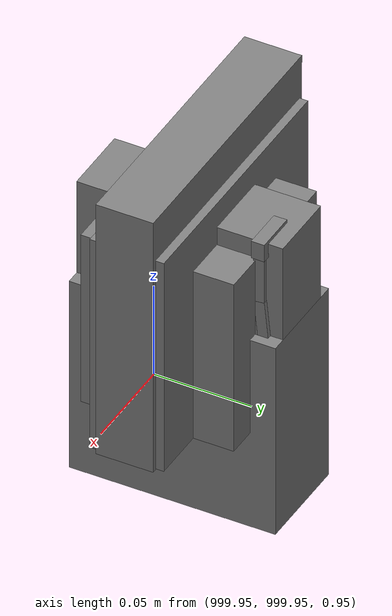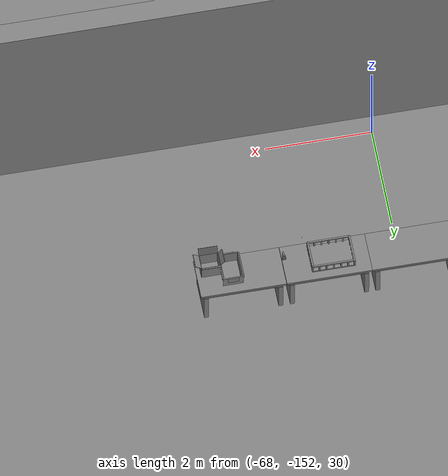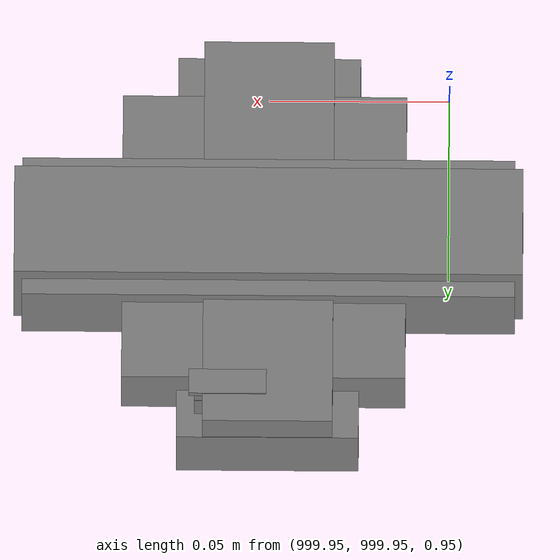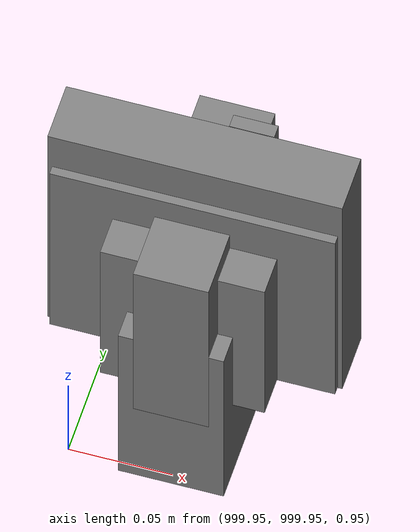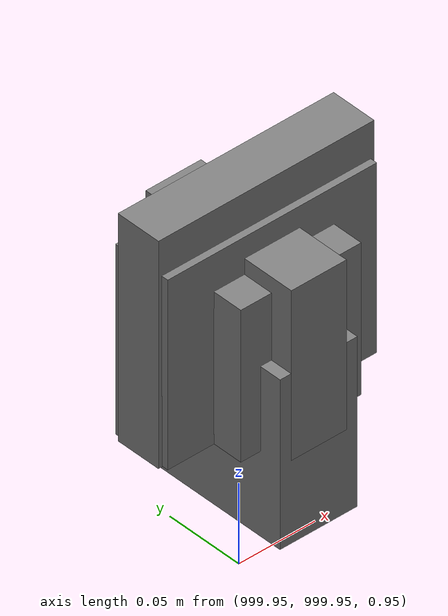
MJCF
<mujoco>
    <option gravity="0.000000000 0.000000000 -9.810000420" timestep="0.0049999999" integrator="implicitfast" density="1.225" viscosity="1.8000001e-05" noslip_iterations="10" iterations="100" sdf_iterations="50">
        <flag multiccd="disable"/>
    </option>
    <size memory="1000M"/>
    <compiler coordinate="local"/>
    <worldbody>
        <light cutoff="30" pos="0 1 1" dir="0 -1 -2"/>
        <light cutoff="30" pos="0 -1 1" dir="0 1 -2"/>
        <body pos="-65.947250366 -149.115768433 31.162775040" euler="121.998260498 11.409472466 -73.529968262" mocap="true" name="spotlight5_SpotLight"/>
        <body pos="1000.000000000 1000.000000000 1.000000000" euler="0.000000000 0.000000000 180.000000000" name="openloong_gripper_2f85_fix_base_usda_wifi_box">
            <geom contype="1" conaffinity="1" density="1000" type="box" material="" rgba="0.500000000 0.500000000 0.500000000 1.000000000" solimp="0.899999976 0.949999988 0.001000000" friction="1.000000000 0.005000000 0.000100000" solref="0.020000000 1.000000000" margin="0" condim="3" group="0" pos="0.000000000 0.000000000 0.058978677" quat="0.000000000 0.000000047 0.000000000 1.000000000" size="0.068499997 0.018999999 0.059000000" name="openloong_gripper_2f85_fix_base_usda_geom_B2DC825E_FA8B_446D_9B7F_8D48F95B9ED5"/>
            <freejoint name="openloong_gripper_2f85_fix_base_usda_wifi_box_joint"/>
            <site size="0.005000000 0.005000000 0.005000000" rgba="0.500000000 0.500000000 0.500000000 1.000000000" pos="0.000000000 0.000000000 0.000000000" quat="0.999961913 0.008726500 0.000000000 0.000000000" group="0" type="sphere" name="openloong_gripper_2f85_fix_base_usda_wifi_boxsite"/>
        </body>
        <body pos="1000.000000000 1000.000000000 1.000000000" euler="0.000011953 0.000005123 -179.999984741" name="openloong_gripper_2f85_fix_base_usda_intel_box">
            <geom contype="1" conaffinity="1" density="1000" type="box" material="" rgba="0.500000000 0.500000000 0.500000000 1.000000000" solimp="0.899999976 0.949999988 0.001000000" friction="1.000000000 0.005000000 0.000100000" solref="0.020000000 1.000000000" margin="0" condim="3" group="0" pos="0.000000000 -0.000067139 0.000082284" quat="0.707106709 0.000000225 0.000000253 0.707106650" size="0.052800003 0.025300000 0.052800003" name="openloong_gripper_2f85_fix_base_usda_geom_B0E7E423_C005_4D91_8195_F1EA24C3D554"/>
            <freejoint name="openloong_gripper_2f85_fix_base_usda_intel_box_joint"/>
            <site size="0.005000000 0.005000000 0.005000000" rgba="0.500000000 0.500000000 0.500000000 1.000000000" pos="0.000000000 0.000000000 0.000000000" quat="0.999961913 0.008726500 0.000000000 0.000000000" group="0" type="sphere" name="openloong_gripper_2f85_fix_base_usda_intel_boxsite"/>
        </body>
        <body pos="-66.324249268 -149.369567871 31.163248062" euler="-24.007972717 65.381286621 154.269714355" mocap="true" name="spotlight2_SpotLight"/>
        <body pos="1000.000000000 999.999938965 1.000000000" euler="0.000000000 0.000000000 180.000000000" name="openloong_gripper_2f85_fix_base_usda_intelcore_i5">
            <geom contype="1" conaffinity="1" density="1000" type="box" material="" rgba="0.500000000 0.500000000 0.500000000 1.000000000" solimp="0.899999976 0.949999988 0.001000000" friction="1.000000000 0.005000000 0.000100000" solref="0.020000000 1.000000000" margin="0" condim="3" group="0" pos="0.000000000 0.000000000 0.051722717" quat="0.707106709 0.000000000 0.000000000 -0.707106769" size="0.052800000 0.018080002 0.052800000" name="openloong_gripper_2f85_fix_base_usda_geom_AA9355E4_BCA6_428A_B4CB_462A171753CB"/>
            <freejoint name="openloong_gripper_2f85_fix_base_usda_intelcore_i5_joint"/>
            <site size="0.005000000 0.005000000 0.005000000" rgba="0.500000000 0.500000000 0.500000000 1.000000000" pos="0.000000000 0.000000000 0.000000000" quat="0.999961913 0.008726534 0.000000000 0.000000000" group="0" type="sphere" name="openloong_gripper_2f85_fix_base_usda_intelcore_i5site"/>
        </body>
        <body pos="1000.000000000 1000.000000000 1.000000000" euler="0.000000000 0.000000000 180.000000000" name="openloong_gripper_2f85_fix_base_usda_cpu_fan">
            <geom contype="1" conaffinity="1" density="1000" type="box" material="" rgba="0.500000000 0.500000000 0.500000000 1.000000000" solimp="0.899999976 0.949999988 0.001000000" friction="1.000000000 0.005000000 0.000100000" solref="0.020000000 1.000000000" margin="0" condim="3" group="0" pos="0.000000000 0.000000000 0.070034981" quat="0.000000000 0.000000000 0.000000000 1.000000000" size="0.070700005 0.014699999 0.070700005" name="openloong_gripper_2f85_fix_base_usda_geom_A0B2EC7D_8B5E_4ADA_9293_4824D6587C77"/>
            <freejoint name="openloong_gripper_2f85_fix_base_usda_cpu_fan_joint"/>
            <site size="0.005000000 0.005000000 0.005000000" rgba="0.500000000 0.500000000 0.500000000 1.000000000" pos="0.000000000 0.000000000 0.000000000" quat="0.999961913 0.008726535 0.000000000 0.000000000" group="0" type="sphere" name="openloong_gripper_2f85_fix_base_usda_cpu_fancsite"/>
        </body>
        <body pos="-66.246543884 -149.080932617 31.167840958" euler="-28.193479538 26.337121964 89.810943604" mocap="true" name="spotlight3_SpotLight"/>
        <body pos="1000.000000000 1000.000000000 1.000000000" euler="0.000000000 0.000000000 180.000000000" name="openloong_gripper_2f85_fix_base_usda_battery_01">
            <geom contype="1" conaffinity="1" density="1000" type="box" material="" rgba="0.500000000 0.500000000 0.500000000 1.000000000" solimp="0.899999976 0.949999988 0.001000000" friction="1.000000000 0.005000000 0.000100000" solref="0.020000000 1.000000000" margin="0" condim="3" group="0" pos="-0.011123657 -0.041940309 0.101691343" quat="1.000000000 0.000000000 0.000000000 0.000000000" size="0.010800000 0.003375000 0.004725000" name="openloong_gripper_2f85_fix_base_usda_geom_91EDF2B9_39C3_4ACF_AFBA_BCB3CEFF2451"/>
            <geom contype="1" conaffinity="1" density="1000" type="box" material="" rgba="0.500000000 0.500000000 0.500000000 1.000000000" solimp="0.899999976 0.949999988 0.001000000" friction="1.000000000 0.005000000 0.000100000" solref="0.020000000 1.000000000" margin="0" condim="3" group="0" pos="-0.010876465 -0.044247437 0.047066893" quat="0.998702705 -0.050920475 0.000000000 0.000000000" size="0.009450001 0.002700000 0.024975000" name="openloong_gripper_2f85_fix_base_usda_geom_C2BF3088_AA4B_4B1D_AB16_18FF9823962E"/>
            <geom contype="1" conaffinity="1" density="1000" type="box" material="" rgba="0.500000000 0.500000000 0.500000000 1.000000000" solimp="0.899999976 0.949999988 0.001000000" friction="1.000000000 0.005000000 0.000100000" solref="0.020000000 1.000000000" margin="0" condim="3" group="0" pos="-0.001235962 -0.000659180 0.047381196" quat="1.000000000 0.000000000 0.000000000 0.000000000" size="0.039420001 0.039150000 0.047250003" name="openloong_gripper_2f85_fix_base_usda_geom_07A24C9F_B304_41AC_8B7E_69B9371F9221"/>
            <geom contype="1" conaffinity="1" density="1000" type="box" material="" rgba="0.500000000 0.500000000 0.500000000 1.000000000" solimp="0.899999976 0.949999988 0.001000000" friction="1.000000000 0.005000000 0.000100000" solref="0.020000000 1.000000000" margin="0" condim="3" group="0" pos="-0.010876465 -0.039138794 0.009851727" quat="1.000000000 0.000000000 0.000000000 0.000000000" size="0.009450001 0.010800000 0.013500000" name="openloong_gripper_2f85_fix_base_usda_geom_2D8B815F_A774_42B7_A3B9_300D85537725"/>
            <geom contype="1" conaffinity="1" density="1000" type="box" material="" rgba="0.500000000 0.500000000 0.500000000 1.000000000" solimp="0.899999976 0.949999988 0.001000000" friction="1.000000000 0.005000000 0.000100000" solref="0.020000000 1.000000000" margin="0" condim="3" group="0" pos="-0.010876465 -0.041528322 0.071508206" quat="1.000000000 0.000000000 0.000000000 0.000000000" size="0.009450001 0.002700000 0.027000001" name="openloong_gripper_2f85_fix_base_usda_geom_B8EE91D8_2092_42AB_B313_A85FF5682862"/>
            <freejoint name="openloong_gripper_2f85_fix_base_usda_battery_01_joint"/>
            <site size="0.005000000 0.005000000 0.005000000" rgba="0.500000000 0.500000000 0.500000000 1.000000000" pos="0.000000000 0.000000000 0.000000000" quat="0.999961913 0.008726500 0.000000000 0.000000000" group="0" type="sphere" name="openloong_gripper_2f85_fix_base_usda_battery_01site"/>
        </body>
        <body pos="-64.866622925 -149.383972168 30.183746338" euler="89.999984741 89.999946594 0.000000000" name="openloong_gripper_2f85_fix_base_usda_bluebox_01">
            <geom contype="1" conaffinity="1" density="1000" type="box" material="" rgba="0.500000000 0.500000000 0.500000000 1.000000000" solimp="0.899999976 0.949999988 0.001000000" friction="1.000000000 0.005000000 0.000100000" solref="0.020000000 1.000000000" margin="0" condim="3" group="0" pos="0.276580811 0.187225342 0.000068665" quat="0.707106948 0.000077471 0.707106352 0.000077486" size="0.100000001 0.057999998 0.010000000" name="openloong_gripper_2f85_fix_base_usda_geom_6DCE84E1_726F_4039_AA99_93494B19ECA9"/>
            <geom contype="1" conaffinity="1" density="1000" type="box" material="" rgba="0.500000000 0.500000000 0.500000000 1.000000000" solimp="0.899999976 0.949999988 0.001000000" friction="1.000000000 0.005000000 0.000100000" solref="0.020000000 1.000000000" margin="0" condim="3" group="0" pos="0.000000000 0.002883911 0.000000000" quat="0.999999881 0.000000000 0.000000000 0.000000000" size="0.254000008 0.003000000 0.172000006" name="openloong_gripper_2f85_fix_base_usda_geom_598268FF_02E6_4545_AAA4_31E59827F1EF"/>
            <geom contype="1" conaffinity="1" density="1000" type="box" material="" rgba="0.500000000 0.500000000 0.500000000 1.000000000" solimp="0.899999976 0.949999988 0.001000000" friction="1.000000000 0.005000000 0.000100000" solref="0.020000000 1.000000000" margin="0" condim="3" group="0" pos="0.000000000 0.124874115 0.173484802" quat="0.999796331 0.020176515 -0.000000015 0.000000030" size="0.259999990 0.119999997 0.007000000" name="openloong_gripper_2f85_fix_base_usda_geom_95472E64_FAFE_4FD4_B3AC_511874CEAC87"/>
            <geom contype="1" conaffinity="1" density="1000" type="box" material="" rgba="0.500000000 0.500000000 0.500000000 1.000000000" solimp="0.899999976 0.949999988 0.001000000" friction="1.000000000 0.005000000 0.000100000" solref="0.020000000 1.000000000" margin="0" condim="3" group="0" pos="0.000000000 0.124874115 -0.173469543" quat="0.999796331 -0.020176545 -0.000000015 0.000000000" size="0.259999990 0.119999997 0.007000000" name="openloong_gripper_2f85_fix_base_usda_geom_775E1744_FC34_40C7_B736_9B46FEBE3290"/>
            <geom contype="1" conaffinity="1" density="1000" type="box" material="" rgba="0.500000000 0.500000000 0.500000000 1.000000000" solimp="0.899999976 0.949999988 0.001000000" friction="1.000000000 0.005000000 0.000100000" solref="0.020000000 1.000000000" margin="0" condim="3" group="0" pos="0.000000000 0.214008331 0.188980103" quat="0.999912977 0.013176724 0.000000015 0.000000000" size="0.259999990 0.029999999 0.012500000" name="openloong_gripper_2f85_fix_base_usda_geom_1748B175_6D28_4778_A98E_9AB0EC8B1235"/>
            <geom contype="1" conaffinity="1" density="1000" type="box" material="" rgba="0.500000000 0.500000000 0.500000000 1.000000000" solimp="0.899999976 0.949999988 0.001000000" friction="1.000000000 0.005000000 0.000100000" solref="0.020000000 1.000000000" margin="0" condim="3" group="0" pos="-0.258361816 0.125289917 0.001876831" quat="0.702796936 -0.020792112 0.710783124 0.020769298" size="0.189999998 0.119999997 0.009000000" name="openloong_gripper_2f85_fix_base_usda_geom_19BE9FD4_FE97_40F1_A1D2_C77156B6BFC7"/>
            <geom contype="1" conaffinity="1" density="1000" type="box" material="" rgba="0.500000000 0.500000000 0.500000000 1.000000000" solimp="0.899999976 0.949999988 0.001000000" friction="1.000000000 0.005000000 0.000100000" solref="0.020000000 1.000000000" margin="0" condim="3" group="0" pos="0.000000000 0.214008331 -0.188980103" quat="0.999912977 -0.013176769 0.000000030 0.000000015" size="0.259999990 0.029999999 0.012500000" name="openloong_gripper_2f85_fix_base_usda_geom_0358C9D7_A03C_4AB2_9770_6863E5E47186"/>
            <geom contype="1" conaffinity="1" density="1000" type="box" material="" rgba="0.500000000 0.500000000 0.500000000 1.000000000" solimp="0.899999976 0.949999988 0.001000000" friction="1.000000000 0.005000000 0.000100000" solref="0.020000000 1.000000000" margin="0" condim="3" group="0" pos="-0.276611328 0.187225342 0.000068665" quat="0.707106650 0.000077441 0.707106709 0.000077456" size="0.100000001 0.057999998 0.010000000" name="openloong_gripper_2f85_fix_base_usda_geom_95DDB87D_47D0_49A0_B6DA_B83BBC27A00C"/>
            <geom contype="1" conaffinity="1" density="1000" type="box" material="" rgba="0.500000000 0.500000000 0.500000000 1.000000000" solimp="0.899999976 0.949999988 0.001000000" friction="1.000000000 0.005000000 0.000100000" solref="0.020000000 1.000000000" margin="0" condim="3" group="0" pos="0.258331299 0.125289917 0.001876831" quat="0.702851415 0.018856421 0.710823774 -0.019329369" size="0.189999998 0.119999997 0.009000000" name="openloong_gripper_2f85_fix_base_usda_geom_CC5BDA5A_B86B_40E0_9407_39D75E9C8A99"/>
            <freejoint name="openloong_gripper_2f85_fix_base_usda_bluebox_01_joint"/>
            <site size="0.005000000 0.005000000 0.005000000" rgba="0.500000000 0.500000000 0.500000000 1.000000000" pos="0.000000000 0.000000000 0.000000000" quat="0.999961913 0.008726534 0.000000000 0.000000000" group="0" type="sphere" name="openloong_gripper_2f85_fix_base_usda_bluebox_01site"/>
        </body>
        <body pos="-64.496299744 -149.491867065 30.235729218" euler="0.000000000 0.000000000 89.999946594" name="openloong_gripper_2f85_fix_base_usda_cardboardbox_01">
            <geom contype="1" conaffinity="1" density="1000" type="box" material="" rgba="0.500000000 0.500000000 0.500000000 1.000000000" solimp="0.899999976 0.949999988 0.001000000" friction="1.000000000 0.005000000 0.000100000" solref="0.020000000 1.000000000" margin="0" condim="3" group="0" pos="-0.003166199 -0.004086494 0.005052090" quat="1.000000000 0.000000000 0.000000000 0.000000000" size="0.142499998 0.177500010 0.005000000" name="openloong_gripper_2f85_fix_base_usda_geom_3F76C3F5_38EE_4459_AB07_E2546824FBD0"/>
            <geom contype="1" conaffinity="1" density="1000" type="box" material="" rgba="0.500000000 0.500000000 0.500000000 1.000000000" solimp="0.899999976 0.949999988 0.001000000" friction="1.000000000 0.005000000 0.000100000" solref="0.020000000 1.000000000" margin="0" condim="3" group="0" pos="-0.003166199 0.170316696 0.150570869" quat="1.000000000 0.000000000 0.000000000 0.000000000" size="0.142499998 0.005000000 0.149999991" name="openloong_gripper_2f85_fix_base_usda_geom_287BAB38_9888_4426_874A_C60ABD1097C7"/>
            <geom contype="1" conaffinity="1" density="1000" type="box" material="" rgba="0.500000000 0.500000000 0.500000000 1.000000000" solimp="0.899999976 0.949999988 0.001000000" friction="1.000000000 0.005000000 0.000100000" solref="0.020000000 1.000000000" margin="0" condim="3" group="0" pos="-0.147399902 -0.005307198 0.150570869" quat="1.000000000 0.000000000 0.000000000 0.000000000" size="0.005000000 0.177500010 0.149999991" name="openloong_gripper_2f85_fix_base_usda_geom_C6C485B8_CFDF_414B_B2B9_C7D02C4B2197"/>
            <geom contype="1" conaffinity="1" density="1000" type="box" material="" rgba="0.500000000 0.500000000 0.500000000 1.000000000" solimp="0.899999976 0.949999988 0.001000000" friction="1.000000000 0.005000000 0.000100000" solref="0.020000000 1.000000000" margin="0" condim="3" group="0" pos="0.140275955 -0.005307198 0.150570869" quat="1.000000000 0.000000000 0.000000000 0.000000000" size="0.005000000 0.177500010 0.149999991" name="openloong_gripper_2f85_fix_base_usda_geom_4F3E1962_4E1A_4BAD_9791_0400A00CA9AD"/>
            <geom contype="1" conaffinity="1" density="1000" type="box" material="" rgba="0.500000000 0.500000000 0.500000000 1.000000000" solimp="0.899999976 0.949999988 0.001000000" friction="1.000000000 0.005000000 0.000100000" solref="0.020000000 1.000000000" margin="0" condim="3" group="0" pos="-0.003166199 -0.181550980 0.150570869" quat="1.000000000 0.000000000 0.000000000 0.000000000" size="0.142499998 0.005000000 0.149999991" name="openloong_gripper_2f85_fix_base_usda_geom_08A0608C_5CBC_4DF0_A24C_3C5DBCD1477E"/>
            <freejoint name="openloong_gripper_2f85_fix_base_usda_cardboardbox_01_joint"/>
            <site size="0.005000000 0.005000000 0.005000000" rgba="0.500000000 0.500000000 0.500000000 1.000000000" pos="0.000000000 0.000000000 0.000000000" quat="0.999961913 0.008726535 0.000000000 0.000000000" group="0" type="sphere" name="openloong_gripper_2f85_fix_base_usda_site_578D72B3_A92B_4B3A_AA4D_1382D3FA160D"/>
            <body pos="0.139160156 -0.004048347 0.301930904" euler="-179.999954224 49.383502960 179.999954224" name="openloong_gripper_2f85_fix_base_usda_A1_006">
                <geom contype="1" conaffinity="1" density="1000" type="box" material="" rgba="0.500000000 0.500000000 0.500000000 1.000000000" solimp="0.899999976 0.949999988 0.001000000" friction="1.000000000 0.005000000 0.000100000" solref="0.020000000 1.000000000" margin="0" condim="3" group="0" pos="-0.071587563 0.000009537 0.001745224" quat="0.999999881 0.000000000 0.000000000 0.000000000" size="0.071249999 0.179999992 0.002500000" name="openloong_gripper_2f85_fix_base_usda_geom_0007FF07_06DA_4EB1_832A_9D19E0175236"/>
                <joint armature="0" stiffness="0.07" damping="0.0099999998" axis="0.000000 1.000000 0.000000" type="hinge" name="openloong_gripper_2f85_fix_base_usda_A1_006"/>
            </body>
            <body pos="-0.145902634 -0.004086494 0.301938057" euler="-180.000000000 -60.000011444 -180.000000000" name="openloong_gripper_2f85_fix_base_usda_A2_006">
                <geom contype="1" conaffinity="1" density="1000" type="box" material="" rgba="0.500000000 0.500000000 0.500000000 1.000000000" solimp="0.899999976 0.949999988 0.001000000" friction="1.000000000 0.005000000 0.000100000" solref="0.020000000 1.000000000" margin="0" condim="3" group="0" pos="0.071268082 0.000009537 0.002717972" quat="0.000002921 0.000000000 -0.000000030 0.999999881" size="0.071249999 0.179999992 0.002500000" name="openloong_gripper_2f85_fix_base_usda_geom_0CD49300_A0A4_4471_A48B_BCEC0D1AA27A"/>
                <joint armature="0" stiffness="0.07" damping="0.0099999998" axis="0.000000 1.000000 0.000000" type="hinge" name="openloong_gripper_2f85_fix_base_usda_A2_006"/>
            </body>
            <body pos="-0.003385544 0.175991058 0.301930904" euler="-125.858116150 -0.000004561 0.000002331" name="openloong_gripper_2f85_fix_base_usda_B2_006">
                <geom contype="1" conaffinity="1" density="1000" type="box" material="" rgba="0.500000000 0.500000000 0.500000000 1.000000000" solimp="0.899999976 0.949999988 0.001000000" friction="1.000000000 0.005000000 0.000100000" solref="0.020000000 1.000000000" margin="0" condim="3" group="0" pos="0.000009537 -0.070939064 -0.002470016" quat="0.999614120 0.027776197 -0.000000015 0.000000030" size="0.137500003 0.064999998 0.005000000" name="openloong_gripper_2f85_fix_base_usda_geom_697C36AB_2BCE_443D_B13E_68AB05F7CB55"/>
                <joint armature="0" stiffness="0.07" damping="0.0099999998" axis="1.000000 0.000000 0.000000" type="hinge" name="openloong_gripper_2f85_fix_base_usda_B2_006"/>
            </body>
            <body pos="-0.003385544 -0.184140205 0.301938057" euler="147.805557251 0.000000000 0.000000000" name="openloong_gripper_2f85_fix_base_usda_B1_006">
                <geom contype="1" conaffinity="1" density="1000" type="box" material="" rgba="0.500000000 0.500000000 0.500000000 1.000000000" solimp="0.899999976 0.949999988 0.001000000" friction="1.000000000 0.005000000 0.000100000" solref="0.020000000 1.000000000" margin="0" condim="3" group="0" pos="-0.000028610 0.070202351 -0.002703667" quat="0.999614179 -0.027776167 0.000000000 0.000000000" size="0.137500003 0.064999998 0.005000000" name="openloong_gripper_2f85_fix_base_usda_geom_CC1AB339_DF08_4830_BA98_D7EA48E6F395"/>
                <joint armature="0" stiffness="0.07" damping="0.0099999998" axis="1.000000 0.000000 0.000000" type="hinge" name="openloong_gripper_2f85_fix_base_usda_B1_006"/>
            </body>
        </body>
        <body pos="-65.882858276 -149.481979370 30.229999542" euler="-64.487716675 0.000000000 0.000000000" name="openloong_gripper_2f85_fix_base_usda_Barcode">
            <geom contype="1" conaffinity="1" density="1000" type="box" material="" rgba="0.500000000 0.500000000 0.500000000 1.000000000" solimp="0.899999976 0.949999988 0.001000000" friction="1.000000000 0.005000000 0.000100000" solref="0.020000000 1.000000000" margin="0" condim="3" group="0" pos="0.000000000 0.013038635 0.001419067" quat="0.000000000 0.000000000 0.000000000 1.000000119" size="0.034000002 0.010000000 0.017999999" name="openloong_gripper_2f85_fix_base_usda_geom_69DD4BC3_1D27_4C9C_90FA_A0093EF11C83"/>
            <geom contype="1" conaffinity="1" density="1000" type="box" material="" rgba="0.500000000 0.500000000 0.500000000 1.000000000" solimp="0.899999976 0.949999988 0.001000000" friction="1.000000000 0.005000000 0.000100000" solref="0.020000000 1.000000000" margin="0" condim="3" group="0" pos="0.000000000 -0.035301208 -0.007095337" quat="0.000000000 0.000000000 -0.043619365 0.999048233" size="0.028999999 0.010000000 0.020000000" name="openloong_gripper_2f85_fix_base_usda_geom_35201421_DEC6_4B0A_9C9E_F2431306E0C5"/>
            <geom contype="1" conaffinity="1" density="1000" type="box" material="" rgba="0.500000000 0.500000000 0.500000000 1.000000000" solimp="0.899999976 0.949999988 0.001000000" friction="1.000000000 0.005000000 0.000100000" solref="0.020000000 1.000000000" margin="0" condim="3" group="0" pos="0.000000000 -0.043411255 -0.011749268" quat="0.922262907 0.386563420 0.000000000 0.000000000" size="0.026000001 0.010000000 0.020000000" name="openloong_gripper_2f85_fix_base_usda_geom_88B15134_C13C_43F0_8404_DA4F45639D81"/>
            <geom contype="1" conaffinity="1" density="1000" type="box" material="" rgba="0.500000000 0.500000000 0.500000000 1.000000000" solimp="0.899999976 0.949999988 0.001000000" friction="1.000000000 0.005000000 0.000100000" solref="0.020000000 1.000000000" margin="0" condim="3" group="0" pos="0.000000000 -0.016967773 -0.031860352" quat="0.000000000 0.000000000 0.000000000 1.000000119" size="0.008000000 0.010000000 0.013000000" name="openloong_gripper_2f85_fix_base_usda_geom_EC0299A7_748C_4BAA_9E85_4BFBE37904E3"/>
            <geom contype="1" conaffinity="1" density="1000" type="box" material="" rgba="0.500000000 0.500000000 0.500000000 1.000000000" solimp="0.899999976 0.949999988 0.001000000" friction="1.000000000 0.005000000 0.000100000" solref="0.020000000 1.000000000" margin="0" condim="3" group="0" pos="0.000000000 -0.001869202 0.000312805" quat="0.953716993 0.300705761 0.000000000 0.000000000" size="0.032000002 0.010000000 0.018999999" name="openloong_gripper_2f85_fix_base_usda_geom_92CC3A6E_1A57_4D79_8297_6AEEC3467AE6"/>
            <geom contype="1" conaffinity="1" density="1000" type="box" material="" rgba="0.500000000 0.500000000 0.500000000 1.000000000" solimp="0.899999976 0.949999988 0.001000000" friction="1.000000000 0.005000000 0.000100000" solref="0.020000000 1.000000000" margin="0" condim="3" group="0" pos="0.000000000 -0.019531250 -0.003173828" quat="0.953716993 0.300705761 0.000000000 0.000000000" size="0.030999999 0.010000000 0.020000000" name="openloong_gripper_2f85_fix_base_usda_geom_707267FF_C97C_4AE8_858A_406E415232DA"/>
            <geom contype="1" conaffinity="1" density="1000" type="box" material="" rgba="0.500000000 0.500000000 0.500000000 1.000000000" solimp="0.899999976 0.949999988 0.001000000" friction="1.000000000 0.005000000 0.000100000" solref="0.020000000 1.000000000" margin="0" condim="3" group="0" pos="0.000000000 -0.035301208 -0.007095337" quat="0.953716993 0.300705761 0.000000000 0.000000000" size="0.028999999 0.010000000 0.020000000" name="openloong_gripper_2f85_fix_base_usda_geom_D2E001D4_0351_4E9A_90C1_3B2054571A85"/>
            <geom contype="1" conaffinity="1" density="1000" type="box" material="" rgba="0.500000000 0.500000000 0.500000000 1.000000000" solimp="0.899999976 0.949999988 0.001000000" friction="1.000000000 0.005000000 0.000100000" solref="0.020000000 1.000000000" margin="0" condim="3" group="0" pos="0.000000000 -0.042617798 -0.071121216" quat="0.000000000 0.000000000 0.000000000 1.000000119" size="0.013000000 0.021000000 0.059999999" name="openloong_gripper_2f85_fix_base_usda_geom_B0C6DC93_5A1C_476A_8E00_D461105CDA1C"/>
            <freejoint name="openloong_gripper_2f85_fix_base_usda_Barcode_joint"/>
            <site size="0.005000000 0.005000000 0.005000000" rgba="0.500000000 0.500000000 0.500000000 1.000000000" pos="0.000000000 0.000000000 0.000000000" quat="1.000000000 0.000000000 0.000000000 0.000000000" group="0" type="sphere" name="openloong_gripper_2f85_fix_base_usda_Barcode_site"/>
        </body>
        <body pos="-66.745018005 -149.392349243 30.184000015" euler="0.000000000 0.000000000 89.999946594" name="[22330243532741]_Basket_01">
            <geom contype="1" conaffinity="1" density="1000" type="box" material="" rgba="0.500000000 0.500000000 0.500000000 1.000000000" solimp="0.899999976 0.949999988 0.001000000" friction="1.000000000 0.005000000 0.000100000" solref="0.020000000 1.000000000" margin="0" condim="3" group="0" pos="-0.052425385 0.389207840 0.089787483" quat="0.707107008 0.000000000 0.000000000 0.707106411" size="0.014249999 0.014249999 0.059999999" name="[22330243532741]_geom_1D402D64_F8A5_4E87_BC42_33AF17C23FC0"/>
            <geom contype="1" conaffinity="1" density="1000" type="box" material="" rgba="0.500000000 0.500000000 0.500000000 1.000000000" solimp="0.899999976 0.949999988 0.001000000" friction="1.000000000 0.005000000 0.000100000" solref="0.020000000 1.000000000" margin="0" condim="3" group="0" pos="0.264015198 -0.133043289 0.089787483" quat="0.707107008 0.000000000 0.000000000 0.707106411" size="0.014249999 0.014249999 0.059999999" name="[22330243532741]_geom_00C510B9_E82E_4F25_850D_C3A306B0F4E4"/>
            <geom contype="1" conaffinity="1" density="1000" type="box" material="" rgba="0.500000000 0.500000000 0.500000000 1.000000000" solimp="0.899999976 0.949999988 0.001000000" friction="1.000000000 0.005000000 0.000100000" solref="0.020000000 1.000000000" margin="0" condim="3" group="0" pos="-0.264015198 -0.265548706 0.089793205" quat="0.707107008 0.000000000 0.000000000 0.707106411" size="0.014249999 0.014249999 0.059999999" name="[22330243532741]_geom_F6C74D0D_73D2_41B5_81A2_7DFEE6AB56B1"/>
            <geom contype="1" conaffinity="1" density="1000" type="box" material="" rgba="0.500000000 0.500000000 0.500000000 1.000000000" solimp="0.899999976 0.949999988 0.001000000" friction="1.000000000 0.005000000 0.000100000" solref="0.020000000 1.000000000" margin="0" condim="3" group="0" pos="-0.160263062 -0.389322281 0.089793205" quat="0.707107008 0.000000000 0.000000000 0.707106411" size="0.014249999 0.014249999 0.059999999" name="[22330243532741]_geom_00FEC319_1D1D_492D_8566_4EE381BFEB10"/>
            <geom contype="1" conaffinity="1" density="1000" type="box" material="" rgba="0.500000000 0.500000000 0.500000000 1.000000000" solimp="0.899999976 0.949999988 0.001000000" friction="1.000000000 0.005000000 0.000100000" solref="0.020000000 1.000000000" margin="0" condim="3" group="0" pos="0.162265778 -0.389322281 0.089787483" quat="0.707107008 0.000000000 0.000000000 0.707106411" size="0.014249999 0.014249999 0.059999999" name="[22330243532741]_geom_86BD38CD_4C02_4A03_B5D3_F2668D99826A"/>
            <geom contype="1" conaffinity="1" density="1000" type="box" material="" rgba="0.500000000 0.500000000 0.500000000 1.000000000" solimp="0.899999976 0.949999988 0.001000000" friction="1.000000000 0.005000000 0.000100000" solref="0.020000000 1.000000000" margin="0" condim="3" group="0" pos="0.264015198 0.389207840 0.089787483" quat="0.707107008 0.000000000 0.000000000 0.707106411" size="0.014249999 0.014249999 0.059999999" name="[22330243532741]_geom_F442BB7F_3EBB_432F_9451_42F61346B33A"/>
            <geom contype="1" conaffinity="1" density="1000" type="box" material="" rgba="0.500000000 0.500000000 0.500000000 1.000000000" solimp="0.899999976 0.949999988 0.001000000" friction="1.000000000 0.005000000 0.000100000" solref="0.020000000 1.000000000" margin="0" condim="3" group="0" pos="-0.264015198 -0.133043289 0.089793205" quat="0.707107008 0.000000000 0.000000000 0.707106411" size="0.014249999 0.014249999 0.059999999" name="[22330243532741]_geom_156B31C2_C333_479F_9BFF_187B8C7633C7"/>
            <geom contype="1" conaffinity="1" density="1000" type="box" material="" rgba="0.500000000 0.500000000 0.500000000 1.000000000" solimp="0.899999976 0.949999988 0.001000000" friction="1.000000000 0.005000000 0.000100000" solref="0.020000000 1.000000000" margin="0" condim="3" group="0" pos="-0.264026642 0.269256592 0.089793205" quat="0.707107008 0.000000000 0.000000000 0.707106411" size="0.014249999 0.014249999 0.059999999" name="[22330243532741]_geom_5665CE85_D52A_4CFA_836E_AE79C2DE2DBB"/>
            <geom contype="1" conaffinity="1" density="1000" type="box" material="" rgba="0.500000000 0.500000000 0.500000000 1.000000000" solimp="0.899999976 0.949999988 0.001000000" friction="1.000000000 0.005000000 0.000100000" solref="0.020000000 1.000000000" margin="0" condim="3" group="0" pos="0.054462433 0.389207840 0.089787483" quat="0.707107008 0.000000000 0.000000000 0.707106411" size="0.014249999 0.014249999 0.059999999" name="[22330243532741]_geom_BEFD3358_5F7C_4159_9D22_C8A01E2CC4A4"/>
            <geom contype="1" conaffinity="1" density="1000" type="box" material="" rgba="0.500000000 0.500000000 0.500000000 1.000000000" solimp="0.899999976 0.949999988 0.001000000" friction="1.000000000 0.005000000 0.000100000" solref="0.020000000 1.000000000" margin="0" condim="3" group="0" pos="0.054462433 -0.389322281 0.089787483" quat="0.707107008 0.000000000 0.000000000 0.707106411" size="0.014249999 0.014249999 0.059999999" name="[22330243532741]_geom_E71A2B43_3ED4_4D6A_A97B_08EEB58907B7"/>
            <geom contype="1" conaffinity="1" density="1000" type="box" material="" rgba="0.500000000 0.500000000 0.500000000 1.000000000" solimp="0.899999976 0.949999988 0.001000000" friction="1.000000000 0.005000000 0.000100000" solref="0.020000000 1.000000000" margin="0" condim="3" group="0" pos="0.264015198 0.269256592 0.089793205" quat="0.707107008 0.000000000 0.000000000 0.707106411" size="0.014249999 0.014249999 0.059999999" name="[22330243532741]_geom_630C2979_22DD_40C8_B606_F49BAE612D85"/>
            <geom contype="1" conaffinity="1" density="1000" type="box" material="" rgba="0.500000000 0.500000000 0.500000000 1.000000000" solimp="0.899999976 0.949999988 0.001000000" friction="1.000000000 0.005000000 0.000100000" solref="0.020000000 1.000000000" margin="0" condim="3" group="0" pos="0.264015198 -0.389322281 0.089787483" quat="0.707107008 0.000000000 0.000000000 0.707106411" size="0.014249999 0.014249999 0.059999999" name="[22330243532741]_geom_48FEDC94_FE8F_41C3_9293_71D3735E6D77"/>
            <geom contype="1" conaffinity="1" density="1000" type="box" material="" rgba="0.500000000 0.500000000 0.500000000 1.000000000" solimp="0.899999976 0.949999988 0.001000000" friction="1.000000000 0.005000000 0.000100000" solref="0.020000000 1.000000000" margin="0" condim="3" group="0" pos="0.000000000 0.000000000 0.015998840" quat="0.707107008 0.000000000 0.000000000 0.707106411" size="0.403499991 0.279000014 0.015750000" name="[22330243532741]_geom_E701C07B_3216_4359_8C19_AA6802147A23"/>
            <geom contype="1" conaffinity="1" density="1000" type="box" material="" rgba="0.500000000 0.500000000 0.500000000 1.000000000" solimp="0.899999976 0.949999988 0.001000000" friction="1.000000000 0.005000000 0.000100000" solref="0.020000000 1.000000000" margin="0" condim="3" group="0" pos="0.000000000 -0.389476776 0.163619041" quat="0.707107008 0.000000000 0.000000000 0.707106411" size="0.015000000 0.277500004 0.015750000" name="[22330243532741]_geom_E00B6530_EC64_4B37_9D3B_A4C2D5FCA586"/>
            <geom contype="1" conaffinity="1" density="1000" type="box" material="" rgba="0.500000000 0.500000000 0.500000000 1.000000000" solimp="0.899999976 0.949999988 0.001000000" friction="1.000000000 0.005000000 0.000100000" solref="0.020000000 1.000000000" margin="0" condim="3" group="0" pos="0.162265778 0.389207840 0.089787483" quat="0.707107008 0.000000000 0.000000000 0.707106411" size="0.014249999 0.014249999 0.059999999" name="[22330243532741]_geom_511AECD2_D86D_4F3B_9564_7795134772D6"/>
            <geom contype="1" conaffinity="1" density="1000" type="box" material="" rgba="0.500000000 0.500000000 0.500000000 1.000000000" solimp="0.899999976 0.949999988 0.001000000" friction="1.000000000 0.005000000 0.000100000" solref="0.020000000 1.000000000" margin="0" condim="3" group="0" pos="0.000000000 0.389471054 0.163619041" quat="0.707107008 0.000000000 0.000000000 0.707106411" size="0.015000000 0.277500004 0.015750000" name="[22330243532741]_geom_A839339A_B366_4456_BD5B_4E7DE9E76392"/>
            <geom contype="1" conaffinity="1" density="1000" type="box" material="" rgba="0.500000000 0.500000000 0.500000000 1.000000000" solimp="0.899999976 0.949999988 0.001000000" friction="1.000000000 0.005000000 0.000100000" solref="0.020000000 1.000000000" margin="0" condim="3" group="0" pos="-0.263511658 0.000000000 0.163619041" quat="0.707107008 0.000000000 0.000000000 0.707106411" size="0.403499991 0.015000000 0.015750000" name="[22330243532741]_geom_A7B89B85_C159_4000_9B79_83D8C14896FE"/>
            <geom contype="1" conaffinity="1" density="1000" type="box" material="" rgba="0.500000000 0.500000000 0.500000000 1.000000000" solimp="0.899999976 0.949999988 0.001000000" friction="1.000000000 0.005000000 0.000100000" solref="0.020000000 1.000000000" margin="0" condim="3" group="0" pos="-0.264015198 0.141334534 0.089793205" quat="0.707107008 0.000000000 0.000000000 0.707106411" size="0.014249999 0.014249999 0.059999999" name="[22330243532741]_geom_EC1AA04B_3EE9_4F7E_A9FF_36EA69C07752"/>
            <geom contype="1" conaffinity="1" density="1000" type="box" material="" rgba="0.500000000 0.500000000 0.500000000 1.000000000" solimp="0.899999976 0.949999988 0.001000000" friction="1.000000000 0.005000000 0.000100000" solref="0.020000000 1.000000000" margin="0" condim="3" group="0" pos="0.264015198 -0.265548706 0.089787483" quat="0.707107008 0.000000000 0.000000000 0.707106411" size="0.014249999 0.014249999 0.059999999" name="[22330243532741]_geom_F3C3F9A9_D4FF_4E59_897F_BD8D7E4AF599"/>
            <geom contype="1" conaffinity="1" density="1000" type="box" material="" rgba="0.500000000 0.500000000 0.500000000 1.000000000" solimp="0.899999976 0.949999988 0.001000000" friction="1.000000000 0.005000000 0.000100000" solref="0.020000000 1.000000000" margin="0" condim="3" group="0" pos="-0.160263062 0.389207840 0.089787483" quat="0.707107008 0.000000000 0.000000000 0.707106411" size="0.014249999 0.014249999 0.059999999" name="[22330243532741]_geom_4C6D7E06_BF5E_4911_B6C9_3304AEC00490"/>
            <geom contype="1" conaffinity="1" density="1000" type="box" material="" rgba="0.500000000 0.500000000 0.500000000 1.000000000" solimp="0.899999976 0.949999988 0.001000000" friction="1.000000000 0.005000000 0.000100000" solref="0.020000000 1.000000000" margin="0" condim="3" group="0" pos="-0.052425385 -0.389322281 0.089787483" quat="0.707107008 0.000000000 0.000000000 0.707106411" size="0.014249999 0.014249999 0.059999999" name="[22330243532741]_geom_75CF172F_939F_481F_8882_3327BDEABFEF"/>
            <geom contype="1" conaffinity="1" density="1000" type="box" material="" rgba="0.500000000 0.500000000 0.500000000 1.000000000" solimp="0.899999976 0.949999988 0.001000000" friction="1.000000000 0.005000000 0.000100000" solref="0.020000000 1.000000000" margin="0" condim="3" group="0" pos="-0.264026642 -0.389322281 0.089793205" quat="0.707107008 0.000000000 0.000000000 0.707106411" size="0.014249999 0.014249999 0.059999999" name="[22330243532741]_geom_9A330F3F_7F0F_42E7_9F34_BB5D112EFBEE"/>
            <geom contype="1" conaffinity="1" density="1000" type="box" material="" rgba="0.500000000 0.500000000 0.500000000 1.000000000" solimp="0.899999976 0.949999988 0.001000000" friction="1.000000000 0.005000000 0.000100000" solref="0.020000000 1.000000000" margin="0" condim="3" group="0" pos="0.264015198 0.141334534 0.089787483" quat="0.707107008 0.000000000 0.000000000 0.707106411" size="0.014249999 0.014249999 0.059999999" name="[22330243532741]_geom_FE01638B_15F1_4A1C_92D6_69602B020E07"/>
            <geom contype="1" conaffinity="1" density="1000" type="box" material="" rgba="0.500000000 0.500000000 0.500000000 1.000000000" solimp="0.899999976 0.949999988 0.001000000" friction="1.000000000 0.005000000 0.000100000" solref="0.020000000 1.000000000" margin="0" condim="3" group="0" pos="-0.264015198 0.389207840 0.089793205" quat="0.707107008 0.000000000 0.000000000 0.707106411" size="0.014249999 0.014249999 0.059999999" name="[22330243532741]_geom_4D34C35D_444D_4DFA_BA00_4B885F06C011"/>
            <geom contype="1" conaffinity="1" density="1000" type="box" material="" rgba="0.500000000 0.500000000 0.500000000 1.000000000" solimp="0.899999976 0.949999988 0.001000000" friction="1.000000000 0.005000000 0.000100000" solref="0.020000000 1.000000000" margin="0" condim="3" group="0" pos="0.264015198 0.004480362 0.089787483" quat="0.707107008 0.000000000 0.000000000 0.707106411" size="0.014249999 0.014249999 0.059999999" name="[22330243532741]_geom_10FD4FE1_0BE5_4D87_8688_66FAB149A22D"/>
            <geom contype="1" conaffinity="1" density="1000" type="box" material="" rgba="0.500000000 0.500000000 0.500000000 1.000000000" solimp="0.899999976 0.949999988 0.001000000" friction="1.000000000 0.005000000 0.000100000" solref="0.020000000 1.000000000" margin="0" condim="3" group="0" pos="0.263694763 -0.000011444 0.163619041" quat="0.707107008 0.000000000 0.000000000 0.707106411" size="0.403499991 0.015000000 0.015750000" name="[22330243532741]_geom_B058C98E_FB29_4C4E_BEA8_6E4A33392556"/>
            <geom contype="1" conaffinity="1" density="1000" type="box" material="" rgba="0.500000000 0.500000000 0.500000000 1.000000000" solimp="0.899999976 0.949999988 0.001000000" friction="1.000000000 0.005000000 0.000100000" solref="0.020000000 1.000000000" margin="0" condim="3" group="0" pos="-0.264015198 0.004480362 0.089793205" quat="0.707107008 0.000000000 0.000000000 0.707106411" size="0.014249999 0.014249999 0.059999999" name="[22330243532741]_geom_D776041D_461C_41DB_A11C_CF22C53EF3AB"/>
            <freejoint name="[22330243532741]_joint_275247C2_0DE3_414D_B5DD_31068043764E"/>
        </body>
        <body pos="0.000000000 0.000000000 0.000000000" euler="0.000000000 0.000000000 0.000000000" name="Static Objects_Static Objects">
            <geom contype="1" conaffinity="1" density="1000" type="box" material="" rgba="0.500000000 0.500000000 0.500000000 1.000000000" solimp="0.899999976 0.949999988 0.001000000" friction="1.000000000 0.005000000 0.000100000" solref="0.020000000 1.000000000" margin="0" condim="3" group="0" pos="-67.544113159 -149.365814209 29.727830887" quat="0.500000417 0.499999970 0.499999553 0.499999970" size="0.381000012 0.319999993 0.041000001" name="Static Objects_geom_FB4BAA60_023B_4669_B30B_6F0E998AF5D1"/>
            <geom contype="1" conaffinity="1" density="1000" type="box" material="" rgba="0.500000000 0.500000000 0.500000000 1.000000000" solimp="0.899999976 0.949999988 0.001000000" friction="1.000000000 0.005000000 0.000100000" solref="0.020000000 1.000000000" margin="0" condim="3" group="0" pos="-68.239501953 -149.365814209 30.086868286" quat="0.500000417 0.499999970 0.499999553 0.499999970" size="0.370999992 0.039500002 0.745000005" name="Static Objects_geom_7EA7B6EE_F907_4EA7_88BA_EE1E40FF3E59"/>
            <geom contype="1" conaffinity="1" density="1000" type="box" material="" rgba="0.500000000 0.500000000 0.500000000 1.000000000" solimp="0.899999976 0.949999988 0.001000000" friction="1.000000000 0.005000000 0.000100000" solref="0.020000000 1.000000000" margin="0" condim="3" group="0" pos="-68.239501953 -149.365814209 30.147235870" quat="0.500000417 0.499999970 0.499999553 0.499999970" size="0.400000006 0.022000000 0.800000012" name="Static Objects_geom_C18C572C_CDCE_401F_BC5A_84562DF463CD"/>
            <geom contype="1" conaffinity="1" density="1000" type="box" material="" rgba="0.500000000 0.500000000 0.500000000 1.000000000" solimp="0.899999976 0.949999988 0.001000000" friction="1.000000000 0.005000000 0.000100000" solref="0.020000000 1.000000000" margin="0" condim="3" group="0" pos="-68.934890747 -149.365814209 29.727830887" quat="0.500000417 0.499999970 0.499999553 0.499999970" size="0.381000012 0.319999993 0.041000001" name="Static Objects_geom_D972326D_E05C_44F4_B633_AAF44A6E4589"/>
            <geom contype="1" conaffinity="1" density="1000" type="box" material="" rgba="0.500000000 0.500000000 0.500000000 1.000000000" solimp="0.899999976 0.949999988 0.001000000" friction="1.000000000 0.005000000 0.000100000" solref="0.020000000 1.000000000" margin="0" condim="3" group="0" pos="-68.239501953 -149.365814209 29.561563492" quat="0.500000417 0.499999970 0.499999553 0.499999970" size="0.020000000 0.022000000 0.660000026" name="Static Objects_geom_8A4ACDF0_E422_418B_BEB0_8A67D660AC87"/>
            <geom contype="1" conaffinity="1" density="1000" type="box" material="" rgba="0.500000000 0.500000000 0.500000000 1.000000000" solimp="0.899999976 0.949999988 0.001000000" friction="1.000000000 0.005000000 0.000100000" solref="0.020000000 1.000000000" margin="0" condim="3" group="0" pos="-65.945671082 -149.365814209 29.727830887" quat="0.500000417 0.499999970 0.499999553 0.499999970" size="0.381000012 0.319999993 0.041000001" name="Static Objects_geom_511C1E51_FBE7_4954_8D73_02104F059D76"/>
            <geom contype="1" conaffinity="1" density="1000" type="box" material="" rgba="0.500000000 0.500000000 0.500000000 1.000000000" solimp="0.899999976 0.949999988 0.001000000" friction="1.000000000 0.005000000 0.000100000" solref="0.020000000 1.000000000" margin="0" condim="3" group="0" pos="-66.641059875 -149.365814209 30.086868286" quat="0.500000417 0.499999970 0.499999553 0.499999970" size="0.370999992 0.039500002 0.745000005" name="Static Objects_geom_D52243A5_BD94_4FA7_AFA7_E36D1841C4E6"/>
            <geom contype="1" conaffinity="1" density="1000" type="box" material="" rgba="0.500000000 0.500000000 0.500000000 1.000000000" solimp="0.899999976 0.949999988 0.001000000" friction="1.000000000 0.005000000 0.000100000" solref="0.020000000 1.000000000" margin="0" condim="3" group="0" pos="-66.641059875 -149.365814209 30.147235870" quat="0.500000417 0.499999970 0.499999553 0.499999970" size="0.400000006 0.022000000 0.800000012" name="Static Objects_geom_F4380E78_5D76_472D_9BC3_4B30A7F9B7A0"/>
            <geom contype="1" conaffinity="1" density="1000" type="box" material="" rgba="0.500000000 0.500000000 0.500000000 1.000000000" solimp="0.899999976 0.949999988 0.001000000" friction="1.000000000 0.005000000 0.000100000" solref="0.020000000 1.000000000" margin="0" condim="3" group="0" pos="-67.336448669 -149.365814209 29.727830887" quat="0.500000417 0.499999970 0.499999553 0.499999970" size="0.381000012 0.319999993 0.041000001" name="Static Objects_geom_A2C2589A_B613_4B1F_A24C_A864A0A21B45"/>
            <geom contype="1" conaffinity="1" density="1000" type="box" material="" rgba="0.500000000 0.500000000 0.500000000 1.000000000" solimp="0.899999976 0.949999988 0.001000000" friction="1.000000000 0.005000000 0.000100000" solref="0.020000000 1.000000000" margin="0" condim="3" group="0" pos="-66.641059875 -149.365814209 29.561563492" quat="0.500000417 0.499999970 0.499999553 0.499999970" size="0.020000000 0.022000000 0.660000026" name="Static Objects_geom_F30336B7_856D_4C11_A9C5_18D2DDB9F537"/>
            <geom contype="1" conaffinity="1" density="1000" type="box" material="" rgba="0.500000000 0.500000000 0.500000000 1.000000000" solimp="0.899999976 0.949999988 0.001000000" friction="1.000000000 0.005000000 0.000100000" solref="0.020000000 1.000000000" margin="0" condim="3" group="0" pos="-64.338577271 -149.365814209 29.727830887" quat="0.500000417 0.499999970 0.499999553 0.499999970" size="0.381000012 0.319999993 0.041000001" name="Static Objects_geom_E4ECF624_E633_4C9D_9A43_1A5CCF61B1DA"/>
            <geom contype="1" conaffinity="1" density="1000" type="box" material="" rgba="0.500000000 0.500000000 0.500000000 1.000000000" solimp="0.899999976 0.949999988 0.001000000" friction="1.000000000 0.005000000 0.000100000" solref="0.020000000 1.000000000" margin="0" condim="3" group="0" pos="-65.033966064 -149.365814209 30.086868286" quat="0.500000417 0.499999970 0.499999553 0.499999970" size="0.370999992 0.039500002 0.745000005" name="Static Objects_geom_D1A01FFE_75A8_4980_A518_284B58D91E82"/>
            <geom contype="1" conaffinity="1" density="1000" type="box" material="" rgba="0.500000000 0.500000000 0.500000000 1.000000000" solimp="0.899999976 0.949999988 0.001000000" friction="1.000000000 0.005000000 0.000100000" solref="0.020000000 1.000000000" margin="0" condim="3" group="0" pos="-65.033966064 -149.365814209 30.147235870" quat="0.500000417 0.499999970 0.499999553 0.499999970" size="0.400000006 0.022000000 0.800000012" name="Static Objects_geom_4BA05183_386B_4C45_83AE_B2E26EA239EA"/>
            <geom contype="1" conaffinity="1" density="1000" type="box" material="" rgba="0.500000000 0.500000000 0.500000000 1.000000000" solimp="0.899999976 0.949999988 0.001000000" friction="1.000000000 0.005000000 0.000100000" solref="0.020000000 1.000000000" margin="0" condim="3" group="0" pos="-65.729354858 -149.365814209 29.727830887" quat="0.500000417 0.499999970 0.499999553 0.499999970" size="0.381000012 0.319999993 0.041000001" name="Static Objects_geom_ACDA5EB3_5816_4881_978D_02A37B3E5467"/>
            <geom contype="1" conaffinity="1" density="1000" type="box" material="" rgba="0.500000000 0.500000000 0.500000000 1.000000000" solimp="0.899999976 0.949999988 0.001000000" friction="1.000000000 0.005000000 0.000100000" solref="0.020000000 1.000000000" margin="0" condim="3" group="0" pos="-65.033966064 -149.365814209 29.561563492" quat="0.500000417 0.499999970 0.499999553 0.499999970" size="0.020000000 0.022000000 0.660000026" name="Static Objects_geom_F07F6BB8_04E0_4E41_8238_1D4F94D28255"/>
            <geom contype="1" conaffinity="1" density="1000" type="box" material="" rgba="0.500000000 0.500000000 0.500000000 1.000000000" solimp="0.899999976 0.949999988 0.001000000" friction="1.000000000 0.005000000 0.000100000" solref="0.020000000 1.000000000" margin="0" condim="3" group="0" pos="-61.754566193 -137.853729248 33.906845093" quat="0.707107067 0.000000000 0.000000000 0.707106471" size="0.759999990 0.759999990 4.500000000" name="Static Objects_geom_6EB0F2B0_8133_428C_AD54_211C6C9BE905"/>
            <geom contype="1" conaffinity="1" density="1000" type="box" material="" rgba="0.500000000 0.500000000 0.500000000 1.000000000" solimp="0.899999976 0.949999988 0.001000000" friction="1.000000000 0.005000000 0.000100000" solref="0.020000000 1.000000000" margin="0" condim="3" group="0" pos="-57.511135101 -144.927108765 31.707921982" quat="1.000000000 0.000000000 0.000000000 0.000000000" size="0.200000003 8.000000000 2.299999952" name="Static Objects_geom_877DE95A_022A_41EC_95CA_79AAAC2ADBE0"/>
            <geom contype="1" conaffinity="1" density="1000" type="box" material="" rgba="0.500000000 0.500000000 0.500000000 1.000000000" solimp="0.899999976 0.949999988 0.001000000" friction="1.000000000 0.005000000 0.000100000" solref="0.020000000 1.000000000" margin="0" condim="3" group="0" pos="-80.517646790 -157.574050903 31.688196182" quat="0.707107067 0.000000000 0.000000000 0.707106471" size="0.600000024 0.600000024 2.299999952" name="Static Objects_geom_50986CD8_1036_43DD_88CF_9234268847A8"/>
            <geom contype="1" conaffinity="1" density="1000" type="box" material="" rgba="0.500000000 0.500000000 0.500000000 1.000000000" solimp="0.899999976 0.949999988 0.001000000" friction="1.000000000 0.005000000 0.000100000" solref="0.020000000 1.000000000" margin="0" condim="3" group="0" pos="-80.711044312 -147.414932251 31.666158676" quat="1.000000000 0.000000000 0.000000000 0.000000000" size="0.200000003 10.000000000 2.299999952" name="Static Objects_geom_77811D04_1403_4BAC_93B7_B071C51862FE"/>
            <geom contype="1" conaffinity="1" density="1000" type="box" material="" rgba="0.500000000 0.500000000 0.500000000 1.000000000" solimp="0.899999976 0.949999988 0.001000000" friction="1.000000000 0.005000000 0.000100000" solref="0.020000000 1.000000000" margin="0" condim="3" group="0" pos="-57.687217712 -137.434692383 31.688196182" quat="0.707107067 0.000000000 0.000000000 0.707106471" size="0.600000024 0.600000024 2.299999952" name="Static Objects_geom_2E3B4DE7_9791_4590_BD1C_449E1CCF86F5"/>
            <geom contype="1" conaffinity="1" density="1000" type="box" material="" rgba="0.500000000 0.500000000 0.500000000 1.000000000" solimp="0.899999976 0.949999988 0.001000000" friction="1.000000000 0.005000000 0.000100000" solref="0.020000000 1.000000000" margin="0" condim="3" group="0" pos="-69.537033081 -140.263229370 31.714921951" quat="0.707107067 0.000000000 0.000000000 0.707106471" size="0.759999990 4.500000000 2.299999952" name="Static Objects_geom_2437B8F2_881F_415C_872C_BDDFAEED16FA"/>
            <geom contype="1" conaffinity="1" density="1000" type="box" material="" rgba="0.500000000 0.500000000 0.500000000 1.000000000" solimp="0.899999976 0.949999988 0.001000000" friction="1.000000000 0.005000000 0.000100000" solref="0.020000000 1.000000000" margin="0" condim="3" group="0" pos="-80.073638916 -137.853713989 33.906845093" quat="0.707107067 0.000000000 0.000000000 0.707106471" size="0.759999990 0.759999990 4.500000000" name="Static Objects_geom_48B4190B_BD74_4EE9_8C2D_B23EA782550E"/>
            <geom contype="1" conaffinity="1" density="1000" type="box" material="" rgba="0.500000000 0.500000000 0.500000000 1.000000000" solimp="0.899999976 0.949999988 0.001000000" friction="1.000000000 0.005000000 0.000100000" solref="0.020000000 1.000000000" margin="0" condim="3" group="0" pos="-73.406707764 -155.734664917 31.707921982" quat="1.000000000 0.000000000 0.000000000 0.000000000" size="0.200000003 3.000000000 2.299999952" name="Static Objects_geom_C7E9E099_2887_45B7_882D_DA67AD21EE76"/>
            <geom contype="1" conaffinity="1" density="1000" type="box" material="" rgba="0.500000000 0.500000000 0.500000000 1.000000000" solimp="0.899999976 0.949999988 0.001000000" friction="1.000000000 0.005000000 0.000100000" solref="0.020000000 1.000000000" margin="0" condim="3" group="0" pos="-68.497543335 -137.448257446 31.707921982" quat="0.707107067 0.000000000 0.000000000 0.707106471" size="0.200000003 14.000000000 2.299999952" name="Static Objects_geom_A121E139_E5F5_4721_A09D_AFB1E3FB6666"/>
            <geom contype="1" conaffinity="1" density="1000" type="cylinder" material="" rgba="0.500000000 0.500000000 0.500000000 1.000000000" solimp="0.899999976 0.949999988 0.001000000" friction="1.000000000 0.005000000 0.000100000" solref="0.020000000 1.000000000" margin="0" condim="3" group="0" pos="-68.868522644 -142.134506226 31.711090088" quat="0.707107067 0.000000000 0.000000000 0.707106471" size="0.509999990 2.299999952 1.000000000" name="Static Objects_geom_88AD4DB7_C62E_464D_95AD_FC3569F792D0"/>
            <geom contype="1" conaffinity="1" density="1000" type="plane" material="" rgba="0.500000000 0.500000000 0.500000000 1.000000000" solimp="0.899999976 0.949999988 0.001000000" friction="1.000000000 0.005000000 0.000100000" solref="0.020000000 1.000000000" margin="0" condim="3" group="0" pos="-72.873703003 -147.131927490 29.409669876" quat="1.000000000 0.000000000 0.000000000 0.000000000" size="18.000000000 14.000000000 1.000000000" name="Static Objects_geom_37743657_250C_4C2C_8CAD_9D846D3FA099"/>
            <geom contype="1" conaffinity="1" density="1000" type="box" material="" rgba="0.500000000 0.500000000 0.500000000 1.000000000" solimp="0.899999976 0.949999988 0.001000000" friction="1.000000000 0.005000000 0.000100000" solref="0.020000000 1.000000000" margin="0" condim="3" group="0" pos="-79.943580627 -157.782272339 31.707921982" quat="0.707107067 0.000000000 0.000000000 0.707106471" size="0.200000003 7.000000000 2.299999952" name="Static Objects_geom_1C04E0D7_1A46_4B30_B575_DE7E90B40E45"/>
            <geom contype="1" conaffinity="1" density="1000" type="box" material="" rgba="0.500000000 0.500000000 0.500000000 1.000000000" solimp="0.899999976 0.949999988 0.001000000" friction="1.000000000 0.005000000 0.000100000" solref="0.020000000 1.000000000" margin="0" condim="3" group="0" pos="-65.421028137 -152.903442383 31.707921982" quat="0.707107067 0.000000000 0.000000000 0.707106471" size="0.200000003 7.800000191 2.299999952" name="Static Objects_geom_8A596042_6811_4424_9383_027B351856CC"/>
            <geom contype="1" conaffinity="1" density="1000" type="box" material="" rgba="0.500000000 0.500000000 0.500000000 1.000000000" solimp="0.899999976 0.949999988 0.001000000" friction="1.000000000 0.005000000 0.000100000" solref="0.020000000 1.000000000" margin="0" condim="3" group="0" pos="-74.776908875 -149.964416504 31.688196182" quat="1.000000000 0.000000000 0.000000000 0.000000000" size="0.600000024 0.409999996 2.299999952" name="Static Objects_geom_D77684E9_56A4_4C36_999A_5D68F1AAC9D0"/>
            <geom contype="1" conaffinity="1" density="1000" type="cylinder" material="" rgba="0.500000000 0.500000000 0.500000000 1.000000000" solimp="0.899999976 0.949999988 0.001000000" friction="1.000000000 0.005000000 0.000100000" solref="0.020000000 1.000000000" margin="0" condim="3" group="0" pos="-60.161884308 -142.134506226 31.711090088" quat="0.707107067 0.000000000 0.000000000 0.707106471" size="0.509999990 2.299999952 1.000000000" name="Static Objects_geom_AB8B59E3_F60C_465F_849E_651C3754B8B7"/>
            <geom contype="1" conaffinity="1" density="1000" type="cylinder" material="" rgba="0.500000000 0.500000000 0.500000000 1.000000000" solimp="0.899999976 0.949999988 0.001000000" friction="1.000000000 0.005000000 0.000100000" solref="0.020000000 1.000000000" margin="0" condim="3" group="0" pos="-75.382453918 -149.963455200 31.711090088" quat="0.707107067 0.000000000 0.000000000 0.707106471" size="0.409999996 2.299999952 1.000000000" name="Static Objects_geom_764A611A_1BCE_428F_A7D8_49015F678AF7"/>
            <geom contype="1" conaffinity="1" density="1000" type="cylinder" material="" rgba="0.500000000 0.500000000 0.500000000 1.000000000" solimp="0.899999976 0.949999988 0.001000000" friction="1.000000000 0.005000000 0.000100000" solref="0.020000000 1.000000000" margin="0" condim="3" group="0" pos="-74.154960632 -149.963455200 31.711090088" quat="0.707107067 0.000000000 0.000000000 0.707106471" size="0.409999996 2.299999952 1.000000000" name="Static Objects_geom_CFF33EB8_F8F7_4DE1_8CF6_68084E31B4E5"/>
            <geom contype="1" conaffinity="1" density="1000" type="cylinder" material="" rgba="0.500000000 0.500000000 0.500000000 1.000000000" solimp="0.899999976 0.949999988 0.001000000" friction="1.000000000 0.005000000 0.000100000" solref="0.020000000 1.000000000" margin="0" condim="3" group="0" pos="-77.566612244 -142.134506226 31.711090088" quat="0.707107067 0.000000000 0.000000000 0.707106471" size="0.509999990 2.299999952 1.000000000" name="Static Objects_geom_143FE768_5D7F_4608_AC86_A8CC0D536414"/>
        </body>
        <body pos="-66.291030884 -149.869689941 29.018842697" euler="0.000000000 0.000000000 89.999946594" mocap="true" name="openloong_gripper_2f85_fix_base_usda_leftHandMocap"/>
        <body pos="-66.291030884 -149.869689941 29.018842697" euler="0.000000000 0.000000000 89.999946594" mocap="true" name="openloong_gripper_2f85_fix_base_usda_rightHandMocap"/>
        <body pos="-66.291030884 -149.869689941 30.218843460" euler="0.000000000 0.000000000 89.999946594" name="openloong_gripper_2f85_fix_base_usda_base_link">
            <geom contype="1" conaffinity="1" density="1000" type="mesh" material="" rgba="0.783999979 0.783999979 0.783999979 1.000000000" solimp="0.899999976 0.949999988 0.001000000" friction="1.000000000 0.005000000 0.000100000" solref="0.020000000 1.000000000" margin="0" condim="3" group="3" mesh="base_link" pos="0.000000000 0.000000000 0.000000000" quat="1.000000000 0.000000000 0.000000000 0.000000000" size="1.000000000 1.000000000 1.000000000" name="openloong_gripper_2f85_fix_base_usda__geom_7_1B1372B8_D692_42DF_B565_F6F09FCDB04C"/>
            <site size="0.005000000 0.005000000 0.005000000" rgba="0.500000000 0.500000000 0.500000000 1.000000000" pos="0.000000000 0.000000000 0.000000000" quat="1.000000000 0.000000000 0.000000000 0.000000000" group="0" type="sphere" name="openloong_gripper_2f85_fix_base_usda_imu"/>
            <inertial mass="22.447001" pos="-0.005664100 -0.001336700 0.238289997" diaginertia="0.374352545 0.277180195 0.220617250" quat="0.999247074 0.035235517 -0.015086859 0.006023135"/>
            <body pos="0.000000000 0.000000000 0.299997330" euler="0.000000000 0.000000000 0.000000000" name="openloong_gripper_2f85_fix_base_usda_dummy_body">
                <geom contype="1" conaffinity="1" density="1000" type="sphere" material="" rgba="0.783999979 0.783999979 0.783999979 1.000000000" solimp="0.899999976 0.949999988 0.001000000" friction="1.000000000 0.005000000 0.000100000" solref="0.020000000 1.000000000" margin="0" condim="3" group="3" pos="0.000000000 0.000000000 0.000000000" quat="1.000000000 0.000000000 0.000000000 0.000000000" size="0.010000000 0.000000000 0.000000000" name="openloong_gripper_2f85_fix_base_usda__geom_8_8ADDB247_07E6_4AC7_93A0_58A98ED831BA"/>
                <joint armature="0.0099999998" stiffness="0" damping="0.1" axis="0.000000 0.000000 1.000000" type="hinge" name="openloong_gripper_2f85_fix_base_usda_dummy_joint"/>
                <site size="0.010000000 0.005000000 0.005000000" rgba="0.500000000 0.500000000 0.500000000 1.000000000" pos="0.000000000 0.000000000 0.000000000" quat="1.000000000 0.000000000 0.000000000 0.000000000" group="3" type="sphere" name="openloong_gripper_2f85_fix_base_usda_dummy_site"/>
            </body>
            <body pos="0.009002686 0.000000000 0.406400681" euler="0.000000000 0.000000000 0.000000000" name="openloong_gripper_2f85_fix_base_usda_Link_head_yaw">
                <geom contype="1" conaffinity="1" density="1000" type="mesh" material="" rgba="0.783999979 0.783999979 0.783999979 1.000000000" solimp="0.899999976 0.949999988 0.001000000" friction="1.000000000 0.005000000 0.000100000" solref="0.020000000 1.000000000" margin="0" condim="3" group="3" mesh="Link_head_yaw" pos="0.000000000 0.000000000 0.000000000" quat="1.000000000 0.000000000 0.000000000 0.000000000" size="1.000000000 1.000000000 1.000000000" name="openloong_gripper_2f85_fix_base_usda__geom_10_38EC4B95_2323_4EF5_9D59_72A73DF3EBB1"/>
                <inertial mass="0.84249002" pos="0.000000000 -0.002081400 0.044801001" diaginertia="0.000700588 0.000629000 0.000553812" quat="0.706933022 -0.015675601 0.015677100 0.706933022"/>
                <body pos="0.000000000 -0.034599304 0.048500061" euler="0.000000000 0.000000000 0.000000000" name="openloong_gripper_2f85_fix_base_usda_Link_head_pitch">
                    <geom contype="1" conaffinity="1" density="1000" type="mesh" material="" rgba="0.783999979 0.783999979 0.783999979 1.000000000" solimp="0.899999976 0.949999988 0.001000000" friction="1.000000000 0.005000000 0.000100000" solref="0.020000000 1.000000000" margin="0" condim="3" group="3" mesh="Link_head_pitch" pos="0.000000000 0.000000000 0.000000000" quat="1.000000000 0.000000000 0.000000000 0.000000000" size="1.000000000 1.000000000 1.000000000" name="openloong_gripper_2f85_fix_base_usda__geom_12_9C391397_6C01_4172_BFE4_C122D435B609"/>
                    <inertial mass="1.3943" pos="0.020569000 0.033004001 0.125000000" diaginertia="0.006381400 0.006289940 0.004481460" quat="0.973390222 0.008406822 0.228157058 0.019624906"/>
                    <body pos="0.000000000 0.029998779 0.000000000" euler="0.000000000 0.000000000 0.000000000" name="openloong_gripper_2f85_fix_base_usda_neck_center_body">
                        <site size="0.010000000 0.005000000 0.005000000" rgba="0.500000000 0.500000000 0.500000000 1.000000000" pos="0.000000000 0.000000000 0.000000000" quat="1.000000000 0.000000000 0.000000000 0.000000000" group="3" type="sphere" name="openloong_gripper_2f85_fix_base_usda_neck_center_site"/>
                        <body pos="0.020004272 0.000000000 0.149999619" euler="-0.000002229 39.998176575 -90.000205994" name="openloong_gripper_2f85_fix_base_usda_camera_head">
                            <site size="0.010000000 0.005000000 0.005000000" rgba="0.500000000 0.500000000 0.500000000 1.000000000" pos="0.000000000 0.000000000 0.000000000" quat="1.000000000 0.000000000 0.000000000 0.000000000" group="3" type="sphere" name="openloong_gripper_2f85_fix_base_usda_camera_head_site"/>
                        </body>
                    </body>
                </body>
            </body>
            <body pos="0.003997803 -0.161598206 0.392200470" euler="0.000000000 0.000000000 0.000000000" name="openloong_gripper_2f85_fix_base_usda_Link_arm_r_01">
                <geom contype="1" conaffinity="1" density="1000" type="mesh" material="" rgba="0.783999979 0.783999979 0.783999979 1.000000000" solimp="0.899999976 0.949999988 0.001000000" friction="1.000000000 0.005000000 0.000100000" solref="0.020000000 1.000000000" margin="0" condim="3" group="3" mesh="Link_arm_r_01" pos="0.000000000 0.000000000 0.000000000" quat="1.000000000 0.000000000 0.000000000 0.000000000" size="1.000000000 1.000000000 1.000000000" name="openloong_gripper_2f85_fix_base_usda__geom_14_E3A517D8_4016_4D04_A230_D79A1870ECD1"/>
                <joint armature="0.0099999998" stiffness="0" damping="1" axis="0.000000 -1.000000 0.000000" limited="true" range="-170.000015259 170.000015259" type="hinge" name="openloong_gripper_2f85_fix_base_usda_J_arm_r_01"/>
                <inertial mass="0.75641" pos="0.004494600 -0.038293999 -0.000001874" diaginertia="0.000842990 0.000803050 0.000587120" quat="-0.000163502 0.707098067 0.000812463 0.707115054"/>
                <body pos="-0.041992188 -0.041000366 0.000000000" euler="0.000000000 0.000000000 0.000000000" name="openloong_gripper_2f85_fix_base_usda_Link_arm_r_02">
                    <geom contype="1" conaffinity="1" density="1000" type="mesh" material="" rgba="0.783999979 0.783999979 0.783999979 1.000000000" solimp="0.899999976 0.949999988 0.001000000" friction="1.000000000 0.005000000 0.000100000" solref="0.020000000 1.000000000" margin="0" condim="3" group="3" mesh="Link_arm_r_02" pos="0.000000000 0.000000000 0.000000000" quat="1.000000000 0.000000000 0.000000000 0.000000000" size="1.000000000 1.000000000 1.000000000" name="openloong_gripper_2f85_fix_base_usda__geom_16_7788F4BE_B29E_44FB_98AE_2CFE52DF392E"/>
                    <joint armature="0.0099999998" stiffness="0" damping="1" axis="-1.000000 0.000000 0.000000" limited="true" range="-105.000244141 105.000244141" type="hinge" name="openloong_gripper_2f85_fix_base_usda_J_arm_r_02"/>
                    <inertial mass="0.98500001" pos="0.041999999 -0.067430697 0.000000000" diaginertia="0.002262690 0.001730990 0.001154020" quat="0.500000000 0.500000000 -0.500000000 0.500000000"/>
                    <body pos="0.041992188 -0.122596741 0.000000000" euler="0.000000000 0.000000000 0.000000000" name="openloong_gripper_2f85_fix_base_usda_Link_arm_r_03">
                        <geom contype="1" conaffinity="1" density="1000" type="mesh" material="" rgba="0.783999979 0.783999979 0.783999979 1.000000000" solimp="0.899999976 0.949999988 0.001000000" friction="1.000000000 0.005000000 0.000100000" solref="0.020000000 1.000000000" margin="0" condim="3" group="3" mesh="Link_arm_r_03" pos="0.000000000 0.000000000 0.000000000" quat="1.000000000 0.000000000 0.000000000 0.000000000" size="1.000000000 1.000000000 1.000000000" name="openloong_gripper_2f85_fix_base_usda__geom_18_EF86FD68_2A9D_4827_A528_A8F72344862E"/>
                        <joint armature="0.0099999998" stiffness="0" damping="1" axis="0.000000 -1.000000 0.000000" limited="true" range="-170.000015259 170.000015259" type="hinge" name="openloong_gripper_2f85_fix_base_usda_J_arm_r_03"/>
                        <inertial mass="0.95899999" pos="-0.001413580 -0.164663002 0.020757901" diaginertia="0.002101340 0.002064590 0.000754802" quat="0.560480952 0.454391927 -0.443732947 0.531497955"/>
                        <body pos="0.035293579 -0.177406311 0.023998260" euler="0.000000000 0.000000000 0.000000000" name="openloong_gripper_2f85_fix_base_usda_Link_arm_r_04">
                            <geom contype="1" conaffinity="1" density="1000" type="mesh" material="" rgba="0.783999979 0.783999979 0.783999979 1.000000000" solimp="0.899999976 0.949999988 0.001000000" friction="1.000000000 0.005000000 0.000100000" solref="0.020000000 1.000000000" margin="0" condim="3" group="3" mesh="Link_arm_r_04" pos="0.000000000 0.000000000 0.000000000" quat="1.000000000 0.000000000 0.000000000 0.000000000" size="1.000000000 1.000000000 1.000000000" name="openloong_gripper_2f85_fix_base_usda__geom_20_97131A54_3175_4665_AD6B_B29D39FC4D2D"/>
                            <joint armature="0.0099999998" stiffness="0" damping="1" axis="-1.000000 0.000000 0.000000" limited="true" range="0.000000000 170.000015259" type="hinge" name="openloong_gripper_2f85_fix_base_usda_J_arm_r_04"/>
                            <inertial mass="0.60000002" pos="-0.038727000 -0.060766999 -0.021003000" diaginertia="0.001092610 0.000712422 0.000645102" quat="0.327701002 0.632602990 -0.467366993 0.523443997"/>
                            <body pos="-0.035293579 -0.103492737 -0.023998260" euler="0.000000000 0.000000000 0.000000000" name="openloong_gripper_2f85_fix_base_usda_Link_arm_r_05">
                                <geom contype="1" conaffinity="1" density="1000" type="mesh" material="" rgba="0.783999979 0.783999979 0.783999979 1.000000000" solimp="0.899999976 0.949999988 0.001000000" friction="1.000000000 0.005000000 0.000100000" solref="0.020000000 1.000000000" margin="0" condim="3" group="3" mesh="Link_arm_r_05" pos="0.000000000 0.000000000 0.000000000" quat="1.000000000 0.000000000 0.000000000 0.000000000" size="1.000000000 1.000000000 1.000000000" name="openloong_gripper_2f85_fix_base_usda__geom_22_48596A58_1A59_4562_9EE4_DA060B8648B4"/>
                                <joint armature="0.0099999998" stiffness="0" damping="1" axis="0.000000 -1.000000 0.000000" limited="true" range="-170.000015259 170.000015259" type="hinge" name="openloong_gripper_2f85_fix_base_usda_J_arm_r_05"/>
                                <inertial mass="0.68976003" pos="0.000032712 -0.068658002 -0.000111780" diaginertia="0.002522510 0.002411100 0.000448695" quat="0.707660973 0.706543028 -0.002603360 0.002470550"/>
                                <body pos="-0.026489258 -0.196502686 0.000000000" euler="0.000000000 0.000000000 0.000000000" name="openloong_gripper_2f85_fix_base_usda_Link_arm_r_06">
                                    <geom contype="1" conaffinity="1" density="1000" type="mesh" material="" rgba="0.783999979 0.783999979 0.783999979 1.000000000" solimp="0.899999976 0.949999988 0.001000000" friction="1.000000000 0.005000000 0.000100000" solref="0.020000000 1.000000000" margin="0" condim="3" group="3" mesh="Link_arm_r_06" pos="0.000000000 0.000000000 0.000000000" quat="1.000000000 0.000000000 0.000000000 0.000000000" size="1.000000000 1.000000000 1.000000000" name="openloong_gripper_2f85_fix_base_usda__geom_24_4EA4D892_236E_4E68_861D_9915AE7D6B04"/>
                                    <joint armature="0.0099999998" stiffness="0" damping="1" axis="1.000000 0.000000 0.000000" limited="true" range="-105.000244141 105.000244141" type="hinge" name="openloong_gripper_2f85_fix_base_usda_J_arm_r_06"/>
                                    <inertial mass="0.28" pos="0.026078001 -0.000000896 0.001663700" diaginertia="0.000156930 0.000145601 0.000104979" quat="0.707080841 0.001851080 0.001883810 0.707127810"/>
                                    <body pos="0.026489258 0.000000000 0.031799316" euler="0.000000000 0.000000000 0.000000000" name="openloong_gripper_2f85_fix_base_usda_Link_arm_r_07">
                                        <geom contype="1" conaffinity="1" density="1000" type="mesh" material="" rgba="0.783999979 0.783999979 0.783999979 1.000000000" solimp="0.899999976 0.949999988 0.001000000" friction="1.000000000 0.005000000 0.000100000" solref="0.020000000 1.000000000" margin="0" condim="3" group="3" mesh="Link_arm_r_07" pos="0.000000000 0.000000000 0.000000000" quat="1.000000000 0.000000000 0.000000000 0.000000000" size="1.000000000 1.000000000 1.000000000" name="openloong_gripper_2f85_fix_base_usda__geom_26_9B0C4E6F_BBE0_469E_961A_DB60507716B9"/>
                                        <joint armature="0.0099999998" stiffness="0" damping="1" axis="0.000000 0.000000 1.000000" limited="true" range="-60.000133514 60.000133514" type="hinge" name="openloong_gripper_2f85_fix_base_usda_J_arm_r_07"/>
                                        <inertial mass="0.61353999" pos="-0.007859000 -0.158170000 -0.027736001" diaginertia="0.003037610 0.002570910 0.000729379" quat="0.427542925 0.443532884 -0.553093910 0.560867906"/>
                                        <body pos="0.000000000 0.286994934 -0.270000458" euler="150.000350952 -0.000001649 -0.000000442" name="openloong_gripper_2f85_fix_base_usda_camera_wrist_r">
                                            <site size="0.010000000 0.005000000 0.005000000" rgba="0.500000000 0.500000000 0.500000000 1.000000000" pos="0.000000000 0.000000000 0.000000000" quat="1.000000000 0.000000000 0.000000000 0.000000000" group="3" type="sphere" name="openloong_gripper_2f85_fix_base_usda_camera_wrist_r_site"/>
                                        </body>
                                        <body pos="0.000000000 -0.220008850 -0.033002853" euler="0.000000000 0.000000000 179.999969482" name="openloong_gripper_2f85_fix_base_usda_ee_center_body_r">
                                            <site size="0.010000000 0.005000000 0.005000000" rgba="0.500000000 0.500000000 0.500000000 1.000000000" pos="0.000000000 0.000000000 0.000000000" quat="1.000000000 0.000000000 0.000000000 0.000000000" group="3" type="sphere" name="openloong_gripper_2f85_fix_base_usda_ee_center_site_r"/>
                                        </body>
                                        <body pos="0.000000000 -0.066001892 -0.031000137" euler="89.999984741 0.000000000 180.000000000" name="openloong_gripper_2f85_fix_base_usda_zbr_base_link">
                                            <geom contype="1" conaffinity="1" density="1000" type="mesh" material="" rgba="0.783999979 0.783999979 0.783999979 1.000000000" solimp="0.899999976 0.949999988 0.001000000" friction="1.000000000 0.005000000 0.000100000" solref="0.020000000 1.000000000" margin="0" condim="3" group="3" mesh="base" pos="0.000000000 0.000003815 -0.000007629" quat="1.000000000 0.000000000 0.000000000 0.000000000" size="1.000000238 1.000000238 1.000000238" name="openloong_gripper_2f85_fix_base_usda__geom_30_EF647B35_C46B_41BB_B77D_16CA54C9CC92"/>
                                            <inertial mass="0.77744102" pos="0.000000000 -0.000027039 0.035467502" diaginertia="0.000260285 0.000225381 0.000152708" quat="0.999998808 -0.001528488 0.000000000 0.000000000"/>
                                            <body pos="-0.030609138 0.004745484 0.065696731" euler="-89.999984741 -0.000000000 0.000000000" name="openloong_gripper_2f85_fix_base_usda_r_left_driver">
                                                <geom contype="1" conaffinity="1" density="1000" type="mesh" material="" rgba="0.783999979 0.783999979 0.783999979 1.000000000" solimp="0.899999976 0.949999988 0.001000000" friction="1.000000000 0.005000000 0.000100000" solref="0.020000000 1.000000000" margin="0" condim="3" group="3" mesh="driver" pos="0.030609138 0.054901138 -0.004699708" quat="0.707106829 0.707106709 0.000000000 -0.000000000" size="1.000000238 1.000000238 1.000000238" name="openloong_gripper_2f85_fix_base_usda__geom_32_820FFCB2_0A6A_46FE_8DD9_4D1676691CED"/>
                                                <joint armature="0.0049999999" stiffness="0" damping="0.1" axis="0.000000 0.000000 1.000000" limited="true" range="0.000000000 51.566200256" type="hinge" name="openloong_gripper_2f85_fix_base_usda_r_left_driver_joint"/>
                                                <inertial mass="0.0089956298" pos="0.000000000 0.017754700 0.001073140" diaginertia="0.000001724 0.000001609 0.000000322" quat="0.681301236 0.732003212 0.000000000 0.000000000"/>
                                                <body pos="-0.031402595 0.004524232 -0.010200503" euler="0.000000000 0.000000000 180.000000000" name="openloong_gripper_2f85_fix_base_usda_r_left_coupler">
                                                    <geom contype="1" conaffinity="1" density="1000" type="mesh" material="" rgba="0.783999979 0.783999979 0.783999979 1.000000000" solimp="0.899999976 0.949999988 0.001000000" friction="1.000000000 0.005000000 0.000100000" solref="0.020000000 1.000000000" margin="0" condim="3" group="3" mesh="coupler" pos="-0.062011734 -0.050354015 0.005500795" quat="0.707106829 -0.707106709 0.000000000 -0.000000000" size="1.000000238 1.000000238 1.000000238" name="openloong_gripper_2f85_fix_base_usda__geom_34_D887EB2E_3125_4980_9B52_FEFA9A68FBBF"/>
                                                    <inertial mass="0.0140974" pos="0.000000000 0.003012090 0.023217499" diaginertia="0.000004162 0.000003522 0.000000888" quat="0.705635548 -0.045590367 0.045590367 0.705635548"/>
                                                </body>
                                            </body>
                                            <body pos="-0.012695315 -0.012001040 0.072212234" euler="-89.999984741 -0.000000000 0.000000000" name="openloong_gripper_2f85_fix_base_usda_r_left_spring_link">
                                                <geom contype="1" conaffinity="1" density="1000" type="mesh" material="" rgba="0.783999979 0.783999979 0.783999979 1.000000000" solimp="0.899999976 0.949999988 0.001000000" friction="1.000000000 0.005000000 0.000100000" solref="0.020000000 1.000000000" margin="0" condim="3" group="3" mesh="spring_link" pos="0.012695315 0.061416641 0.012050631" quat="0.707106829 0.707106709 0.000000000 -0.000000000" size="1.000000238 1.000000238 1.000000238" name="openloong_gripper_2f85_fix_base_usda__geom_36_66AF3DC5_CF3B_469B_9243_951CDA9952E0"/>
                                                <joint armature="0.001" stiffness="0.050000001" damping="0.00125" axis="0.000000 0.000000 1.000000" limited="true" range="-17.000000000 51.566200256" type="hinge" name="openloong_gripper_2f85_fix_base_usda_r_left_spring_link_joint"/>
                                                <inertial mass="0.0221642" pos="-0.000000009 0.018162400 0.021265799" diaginertia="0.000008969 0.000006717 0.000002639" quat="0.663403213 -0.244737089 0.244737089 0.663403213"/>
                                                <body pos="-0.038208015 -0.042503368 0.002950669" euler="180.000000000 0.000000000 -0.002185660" name="openloong_gripper_2f85_fix_base_usda_r_left_follower">
                                                    <geom contype="1" conaffinity="1" density="1000" type="mesh" material="" rgba="0.783999979 0.783999979 0.783999979 1.000000000" solimp="0.899999976 0.949999988 0.001000000" friction="1.000000000 0.005000000 0.000100000" solref="0.020000000 1.000000000" margin="0" condim="3" group="3" mesh="tongue" pos="0.050918590 -0.103920005 -0.009099962" quat="0.707106829 -0.707106709 0.000000030 0.000000030" size="1.000000238 1.000000238 1.000000238" name="openloong_gripper_2f85_fix_base_usda__geom_40_FB3AAE9E_F585_4F21_9BC2_04FDB4869696"/>
                                                    <geom contype="1" conaffinity="1" density="1000" type="mesh" material="" rgba="0.783999979 0.783999979 0.783999979 1.000000000" solimp="0.899999976 0.949999988 0.001000000" friction="1.000000000 0.005000000 0.000100000" solref="0.020000000 1.000000000" margin="0" condim="3" group="3" mesh="follower" pos="0.050918590 -0.103920005 -0.009099962" quat="0.707106829 -0.707106709 0.000000030 0.000000030" size="1.000000238 1.000000238 1.000000238" name="openloong_gripper_2f85_fix_base_usda__geom_39_7769136C_777D_4082_BD5E_DA8C264415AF"/>
                                                    <joint armature="0.001" stiffness="0" damping="0.1" axis="0.000000 0.000000 1.000000" limited="true" range="-49.999961853 51.566200256" type="hinge" name="openloong_gripper_2f85_fix_base_usda_r_left_follower"/>
                                                    <inertial mass="0.0125222" pos="0.000000000 -0.011046000 0.012478600" diaginertia="0.000002674 0.000002456 0.000000602" quat="0.986436546 0.164143041 0.000000000 0.000000000"/>
                                                    <body pos="-0.037765510 -0.103912376 -0.009099962" euler="-89.999984741 0.000000000 0.000004829" name="openloong_gripper_2f85_fix_base_usda_r_left_pad">
                                                        <geom contype="1" conaffinity="1" density="1000" type="box" material="" rgba="0.550000012 0.550000012 0.550000012 1.000000000" solimp="0.949999988 0.990000010 0.001000000" friction="0.699999988 0.005000000 0.000100000" solref="0.020000000 1.000000000" margin="0" condim="3" group="3" mass="1e-06" pos="0.043243419 0.000003815 0.119995147" quat="0.999999881 0.000000000 0.000000000 0.000000000" size="0.002000001 0.011000003 0.009375002" name="openloong_gripper_2f85_fix_base_usda_r_left_pad1_D1F4873C_7A4E_475C_A9D7_C05AE7DFFEF5"/>
                                                        <geom contype="1" conaffinity="1" density="1000" type="box" material="" rgba="0.449999988 0.449999988 0.449999988 1.000000000" solimp="0.949999988 0.990000010 0.001000000" friction="0.600000024 0.005000000 0.000100000" solref="0.020000000 1.000000000" margin="0" condim="3" group="3" mass="1e-06" pos="0.043243419 0.000003815 0.138748199" quat="0.999999881 0.000000000 0.000000000 0.000000000" size="0.002000001 0.011000003 0.009375002" name="openloong_gripper_2f85_fix_base_usda_r_left_pad2_4D8DE5D6_79BF_4307_8FAE_A892C501DE63"/>
                                                    </body>
                                                </body>
                                            </body>
                                            <body pos="0.030593880 -0.004753114 0.065696731" euler="89.999984741 0.000000000 180.000000000" name="openloong_gripper_2f85_fix_base_usda_r_right_driver">
                                                <geom contype="1" conaffinity="1" density="1000" type="mesh" material="" rgba="0.783999979 0.783999979 0.783999979 1.000000000" solimp="0.899999976 0.949999988 0.001000000" friction="1.000000000 0.005000000 0.000100000" solref="0.020000000 1.000000000" margin="0" condim="3" group="3" mesh="driver" pos="0.030593880 0.054901138 -0.004699708" quat="0.707106829 0.707106709 0.000000000 0.000000000" size="1.000000238 1.000000238 1.000000238" name="openloong_gripper_2f85_fix_base_usda__geom_42_428EC444_13D7_41C0_9137_9372FDE80CD3"/>
                                                <joint armature="0.0049999999" stiffness="0" damping="0.1" axis="0.000000 0.000000 1.000000" limited="true" range="0.000000000 51.566200256" type="hinge" name="openloong_gripper_2f85_fix_base_usda_r_right_driver_joint"/>
                                                <inertial mass="0.0089956298" pos="0.000000000 0.017754700 0.001073140" diaginertia="0.000001724 0.000001609 0.000000322" quat="0.681301236 0.732003212 0.000000000 0.000000000"/>
                                                <body pos="-0.031417854 0.004531861 -0.010202411" euler="0.000000000 0.000000000 180.000000000" name="openloong_gripper_2f85_fix_base_usda_r_right_coupler">
                                                    <geom contype="1" conaffinity="1" density="1000" type="mesh" material="" rgba="0.783999979 0.783999979 0.783999979 1.000000000" solimp="0.899999976 0.949999988 0.001000000" friction="1.000000000 0.005000000 0.000100000" solref="0.020000000 1.000000000" margin="0" condim="3" group="3" mesh="coupler" pos="-0.062042251 -0.050376903 0.005500795" quat="0.707106829 -0.707106709 0.000000000 0.000000000" size="1.000000238 1.000000238 1.000000238" name="openloong_gripper_2f85_fix_base_usda__geom_44_692A10B7_4D91_49AC_8D03_B22F2420DA05"/>
                                                    <inertial mass="0.0140974" pos="0.000000000 0.003012090 0.023217499" diaginertia="0.000004162 0.000003522 0.000000888" quat="0.705635548 -0.045590367 0.045590367 0.705635548"/>
                                                </body>
                                            </body>
                                            <body pos="0.012695315 0.011997226 0.072219864" euler="89.999984741 0.000000000 180.000000000" name="openloong_gripper_2f85_fix_base_usda_r_right_spring_link">
                                                <geom contype="1" conaffinity="1" density="1000" type="mesh" material="" rgba="0.783999979 0.783999979 0.783999979 1.000000000" solimp="0.899999976 0.949999988 0.001000000" friction="1.000000000 0.005000000 0.000100000" solref="0.020000000 1.000000000" margin="0" condim="3" group="3" mesh="spring_link" pos="0.012695315 0.061424270 0.012048724" quat="0.707106829 0.707106709 0.000000000 0.000000000" size="1.000000238 1.000000238 1.000000238" name="openloong_gripper_2f85_fix_base_usda__geom_46_A3266BEF_4DC8_47F0_8D4B_FB7F54198D29"/>
                                                <joint armature="0.001" stiffness="0.050000001" damping="0.00125" axis="0.000000 0.000000 1.000000" limited="true" range="-17.000000000 51.566200256" type="hinge" name="openloong_gripper_2f85_fix_base_usda_r_right_spring_link_joint"/>
                                                <inertial mass="0.0221642" pos="-0.000000009 0.018162400 0.021265799" diaginertia="0.000008969 0.000006717 0.000002639" quat="0.663403213 -0.244737089 0.244737089 0.663403213"/>
                                                <body pos="-0.038208015 -0.042495739 0.002950669" euler="180.000000000 0.000000000 0.000000000" name="openloong_gripper_2f85_fix_base_usda_r_right_follower">
                                                    <geom contype="1" conaffinity="1" density="1000" type="mesh" material="" rgba="0.783999979 0.783999979 0.783999979 1.000000000" solimp="0.899999976 0.949999988 0.001000000" friction="1.000000000 0.005000000 0.000100000" solref="0.020000000 1.000000000" margin="0" condim="3" group="3" mesh="follower" pos="0.050888073 -0.103927635 -0.009099962" quat="0.707106829 -0.707106709 0.000000000 0.000000000" size="1.000000238 1.000000238 1.000000238" name="openloong_gripper_2f85_fix_base_usda__geom_50_14488317_5F7F_40EF_8A03_6D75A566B1F2"/>
                                                    <geom contype="1" conaffinity="1" density="1000" type="mesh" material="" rgba="0.783999979 0.783999979 0.783999979 1.000000000" solimp="0.899999976 0.949999988 0.001000000" friction="1.000000000 0.005000000 0.000100000" solref="0.020000000 1.000000000" margin="0" condim="3" group="3" mesh="tongue" pos="0.050888073 -0.103927635 -0.009099962" quat="0.707106829 -0.707106709 0.000000000 0.000000000" size="1.000000238 1.000000238 1.000000238" name="openloong_gripper_2f85_fix_base_usda__geom_49_A15D8A0D_329E_4E80_BBD0_87352E00298B"/>
                                                    <joint armature="0.001" stiffness="0" damping="0.1" axis="0.000000 0.000000 1.000000" limited="true" range="-49.999961853 51.566200256" type="hinge" name="openloong_gripper_2f85_fix_base_usda_r_right_follower_joint"/>
                                                    <inertial mass="0.0125222" pos="0.000000000 -0.011046000 0.012478600" diaginertia="0.000002674 0.000002456 0.000000602" quat="0.986436546 0.164143041 0.000000000 0.000000000"/>
                                                    <body pos="-0.037811287 -0.103927635 -0.009099962" euler="-89.999984741 0.000000000 0.000000000" name="openloong_gripper_2f85_fix_base_usda_r_right_pad">
                                                        <geom contype="1" conaffinity="1" density="1000" type="box" material="" rgba="0.449999988 0.449999988 0.449999988 1.000000000" solimp="0.949999988 0.990000010 0.001000000" friction="0.600000024 0.005000000 0.000100000" solref="0.020000000 1.000000000" margin="0" condim="3" group="3" mass="1e-06" pos="0.043258678 0.000000000 0.138748199" quat="1.000000000 0.000000000 0.000000000 0.000000000" size="0.002000001 0.011000003 0.009375002" name="openloong_gripper_2f85_fix_base_usda_r_right_pad2_CD88BBDC_36FD_4644_A20F_8046BD9C397A"/>
                                                        <geom contype="1" conaffinity="1" density="1000" type="box" material="" rgba="0.550000012 0.550000012 0.550000012 1.000000000" solimp="0.949999988 0.990000010 0.001000000" friction="0.699999988 0.005000000 0.000100000" solref="0.020000000 1.000000000" margin="0" condim="3" group="3" mass="1e-06" pos="0.043258678 0.000003815 0.120002776" quat="1.000000000 0.000000000 0.000000000 0.000000000" size="0.002000001 0.011000003 0.009375002" name="openloong_gripper_2f85_fix_base_usda_r_right_pad1_B506DE35_2F94_4BD7_B0C4_8A6EF5BBEB41"/>
                                                    </body>
                                                </body>
                                            </body>
                                        </body>
                                    </body>
                                </body>
                            </body>
                        </body>
                    </body>
                </body>
            </body>
            <body pos="0.003997803 0.161590576 0.392200470" euler="0.000000000 0.000000000 0.000000000" name="openloong_gripper_2f85_fix_base_usda_Link_arm_l_01">
                <geom contype="1" conaffinity="1" density="1000" type="mesh" material="" rgba="0.783999979 0.783999979 0.783999979 1.000000000" solimp="0.899999976 0.949999988 0.001000000" friction="1.000000000 0.005000000 0.000100000" solref="0.020000000 1.000000000" margin="0" condim="3" group="3" mesh="Link_arm_l_01" pos="0.000000000 0.000000000 0.000000000" quat="1.000000000 0.000000000 0.000000000 0.000000000" size="1.000000000 1.000000000 1.000000000" name="openloong_gripper_2f85_fix_base_usda__geom_52_A6573917_B985_457F_8D47_D50014D3A250"/>
                <joint armature="0.0099999998" stiffness="0" damping="1" axis="0.000000 1.000000 0.000000" limited="true" range="-170.000015259 170.000015259" type="hinge" name="openloong_gripper_2f85_fix_base_usda_J_arm_l_01"/>
                <inertial mass="0.75640601" pos="-0.004494650 0.038294200 -0.000001874" diaginertia="0.000842986 0.000803053 0.000587115" quat="-0.000812496 0.707115054 0.000163424 0.707098067"/>
                <body pos="0.042007446 0.041000366 0.000000000" euler="0.000000000 0.000000000 0.000000000" name="openloong_gripper_2f85_fix_base_usda_Link_arm_l_02">
                    <geom contype="1" conaffinity="1" density="1000" type="mesh" material="" rgba="0.783999979 0.783999979 0.783999979 1.000000000" solimp="0.899999976 0.949999988 0.001000000" friction="1.000000000 0.005000000 0.000100000" solref="0.020000000 1.000000000" margin="0" condim="3" group="3" mesh="Link_arm_l_02" pos="0.000000000 0.000000000 0.000000000" quat="1.000000000 0.000000000 0.000000000 0.000000000" size="1.000000000 1.000000000 1.000000000" name="openloong_gripper_2f85_fix_base_usda__geom_54_8DF9D71D_BBD2_4EBA_B28D_1A7A95FDB6A6"/>
                    <joint armature="0.0099999998" stiffness="0" damping="1" axis="-1.000000 0.000000 0.000000" limited="true" range="-105.000244141 105.000244141" type="hinge" name="openloong_gripper_2f85_fix_base_usda_J_arm_l_02"/>
                    <inertial mass="0.98500001" pos="-0.041999999 0.067430697 0.000000000" diaginertia="0.002262690 0.001730990 0.001154020" quat="0.500000000 0.500000000 -0.500000000 0.500000000"/>
                    <body pos="-0.042007446 0.122596741 0.000000000" euler="0.000000000 0.000000000 0.000000000" name="openloong_gripper_2f85_fix_base_usda_Link_arm_l_03">
                        <geom contype="1" conaffinity="1" density="1000" type="mesh" material="" rgba="0.783999979 0.783999979 0.783999979 1.000000000" solimp="0.899999976 0.949999988 0.001000000" friction="1.000000000 0.005000000 0.000100000" solref="0.020000000 1.000000000" margin="0" condim="3" group="3" mesh="Link_arm_l_03" pos="0.000000000 0.000000000 0.000000000" quat="1.000000000 0.000000000 0.000000000 0.000000000" size="1.000000000 1.000000000 1.000000000" name="openloong_gripper_2f85_fix_base_usda__geom_56_DAF5A133_5C5F_4F0D_8E6D_D05ABBF360BD"/>
                        <joint armature="0.0099999998" stiffness="0" damping="1" axis="0.000000 1.000000 0.000000" limited="true" range="-170.000015259 170.000015259" type="hinge" name="openloong_gripper_2f85_fix_base_usda_J_arm_l_03"/>
                        <inertial mass="0.95899999" pos="0.001413580 0.164663002 0.020757901" diaginertia="0.002101340 0.002064590 0.000754802" quat="0.443732947 0.531497955 -0.560480952 0.454391927"/>
                        <body pos="-0.035293579 0.177406311 0.023998260" euler="0.000000000 0.000000000 0.000000000" name="openloong_gripper_2f85_fix_base_usda_Link_arm_l_04">
                            <geom contype="1" conaffinity="1" density="1000" type="mesh" material="" rgba="0.783999979 0.783999979 0.783999979 1.000000000" solimp="0.899999976 0.949999988 0.001000000" friction="1.000000000 0.005000000 0.000100000" solref="0.020000000 1.000000000" margin="0" condim="3" group="3" mesh="Link_arm_l_04" pos="0.000000000 0.000000000 0.000000000" quat="1.000000000 0.000000000 0.000000000 0.000000000" size="1.000000000 1.000000000 1.000000000" name="openloong_gripper_2f85_fix_base_usda__geom_58_CCE9CD00_F29D_4FB7_ACB7_E3C646F8C6C8"/>
                            <joint armature="0.0099999998" stiffness="0" damping="1" axis="1.000000 0.000000 0.000000" limited="true" range="0.000000000 170.000015259" type="hinge" name="openloong_gripper_2f85_fix_base_usda_J_arm_l_04"/>
                            <inertial mass="0.60000002" pos="0.038727000 0.060767200 -0.021003200" diaginertia="0.001092570 0.000712419 0.000645098" quat="0.467370987 0.523440003 -0.327692002 0.632607996"/>
                            <body pos="0.035293579 0.103500366 -0.023998260" euler="0.000000000 0.000000000 0.000000000" name="openloong_gripper_2f85_fix_base_usda_Link_arm_l_05">
                                <geom contype="1" conaffinity="1" density="1000" type="mesh" material="" rgba="0.783999979 0.783999979 0.783999979 1.000000000" solimp="0.899999976 0.949999988 0.001000000" friction="1.000000000 0.005000000 0.000100000" solref="0.020000000 1.000000000" margin="0" condim="3" group="3" mesh="Link_arm_l_05" pos="0.000000000 0.000000000 0.000000000" quat="1.000000000 0.000000000 0.000000000 0.000000000" size="1.000000000 1.000000000 1.000000000" name="openloong_gripper_2f85_fix_base_usda__geom_60_4F1F3937_92B8_4D7E_8E5C_943916245796"/>
                                <joint armature="0.0099999998" stiffness="0" damping="1" axis="0.000000 1.000000 0.000000" limited="true" range="-170.000015259 170.000015259" type="hinge" name="openloong_gripper_2f85_fix_base_usda_J_arm_l_05"/>
                                <inertial mass="0.68976003" pos="-0.000032712 0.068658002 -0.000111780" diaginertia="0.002522510 0.002411100 0.000448695" quat="0.706543028 0.707660973 0.002470550 -0.002603360"/>
                                <body pos="0.026504517 0.196495056 0.000000000" euler="0.000000000 0.000000000 0.000000000" name="openloong_gripper_2f85_fix_base_usda_Link_arm_l_06">
                                    <geom contype="1" conaffinity="1" density="1000" type="mesh" material="" rgba="0.783999979 0.783999979 0.783999979 1.000000000" solimp="0.899999976 0.949999988 0.001000000" friction="1.000000000 0.005000000 0.000100000" solref="0.020000000 1.000000000" margin="0" condim="3" group="3" mesh="Link_arm_l_06" pos="0.000000000 0.000000000 0.000000000" quat="1.000000000 0.000000000 0.000000000 0.000000000" size="1.000000000 1.000000000 1.000000000" name="openloong_gripper_2f85_fix_base_usda__geom_62_32454343_7137_4272_BD46_5658A7489685"/>
                                    <joint armature="0.0099999998" stiffness="0" damping="1" axis="-1.000000 0.000000 0.000000" limited="true" range="-105.000244141 105.000244141" type="hinge" name="openloong_gripper_2f85_fix_base_usda_J_arm_l_06"/>
                                    <inertial mass="0.28" pos="-0.026077701 0.000000896 0.001663730" diaginertia="0.000156927 0.000145598 0.000104981" quat="0.707080841 -0.001851280 -0.001884020 0.707127810"/>
                                    <body pos="-0.026504517 0.000000000 0.031799316" euler="0.000000000 0.000000000 0.000000000" name="openloong_gripper_2f85_fix_base_usda_Link_arm_l_07">
                                        <geom contype="1" conaffinity="1" density="1000" type="mesh" material="" rgba="0.783999979 0.783999979 0.783999979 1.000000000" solimp="0.899999976 0.949999988 0.001000000" friction="1.000000000 0.005000000 0.000100000" solref="0.020000000 1.000000000" margin="0" condim="3" group="3" mesh="Link_arm_l_07" pos="0.000000000 0.000000000 0.000000000" quat="1.000000000 0.000000000 0.000000000 0.000000000" size="1.000000000 1.000000000 1.000000000" name="openloong_gripper_2f85_fix_base_usda__geom_64_4CF133B8_BEE6_47B4_A4EC_6C876EDDB5BC"/>
                                        <joint armature="0.0099999998" stiffness="0" damping="1" axis="0.000000 0.000000 1.000000" limited="true" range="-60.000133514 60.000133514" type="hinge" name="openloong_gripper_2f85_fix_base_usda_J_arm_l_07"/>
                                        <inertial mass="0.61353999" pos="-0.007787200 0.157049999 -0.027733000" diaginertia="0.003037200 0.002570420 0.000729374" quat="0.443562120 0.427539080 -0.560871124 0.553070128"/>
                                        <body pos="0.000000000 -0.286994934 -0.270000458" euler="-150.000350952 0.000001955 179.976669312" name="openloong_gripper_2f85_fix_base_usda_camera_wrist_l">
                                            <site size="0.010000000 0.005000000 0.005000000" rgba="0.500000000 0.500000000 0.500000000 1.000000000" pos="0.000000000 0.000000000 0.000000000" quat="1.000000000 0.000000000 0.000000000 0.000000000" group="3" type="sphere" name="openloong_gripper_2f85_fix_base_usda_camera_wrist_l_site"/>
                                        </body>
                                        <body pos="0.000000000 0.220008850 -0.033002853" euler="0.000000000 0.000000000 0.000000000" name="openloong_gripper_2f85_fix_base_usda_ee_center_body">
                                            <site size="0.010000000 0.005000000 0.005000000" rgba="0.500000000 0.500000000 0.500000000 1.000000000" pos="0.000000000 0.000000000 0.000000000" quat="1.000000000 0.000000000 0.000000000 0.000000000" group="3" type="sphere" name="openloong_gripper_2f85_fix_base_usda_ee_center_site"/>
                                        </body>
                                        <body pos="0.000000000 0.066009521 -0.031000137" euler="-90.000007629 0.000000000 0.000000000" name="openloong_gripper_2f85_fix_base_usda_zbll_base_link">
                                            <geom contype="1" conaffinity="1" density="1000" type="mesh" material="" rgba="0.783999979 0.783999979 0.783999979 1.000000000" solimp="0.899999976 0.949999988 0.001000000" friction="1.000000000 0.005000000 0.000100000" solref="0.020000000 1.000000000" margin="0" condim="3" group="3" mesh="base" pos="0.000000000 0.000000000 0.000000000" quat="1.000000000 0.000000000 0.000000000 0.000000000" size="1.000000000 1.000000000 1.000000000" name="openloong_gripper_2f85_fix_base_usda__geom_68_8646C36C_12FC_4714_B973_2214005D1A6B"/>
                                            <inertial mass="0.77744102" pos="0.000000000 -0.000027039 0.035467502" diaginertia="0.000260285 0.000225381 0.000152708" quat="0.999998808 -0.001528488 0.000000000 0.000000000"/>
                                            <body pos="-0.030578613 0.004755020 0.065696716" euler="-89.999984741 0.000000000 0.000000000" name="openloong_gripper_2f85_fix_base_usda_l_left_driver">
                                                <geom contype="1" conaffinity="1" density="1000" type="mesh" material="" rgba="0.783999979 0.783999979 0.783999979 1.000000000" solimp="0.899999976 0.949999988 0.001000000" friction="1.000000000 0.005000000 0.000100000" solref="0.020000000 1.000000000" margin="0" condim="3" group="3" mesh="driver" pos="0.030609131 0.054901123 -0.004699707" quat="0.707106829 0.707106709 0.000000000 0.000000000" size="1.000000000 1.000000000 1.000000000" name="openloong_gripper_2f85_fix_base_usda__geom_70_6F1FFDD1_3AF0_4D63_B524_872A1B7C9AEC"/>
                                                <joint armature="0.0049999999" stiffness="0" damping="0.1" axis="0.000000 0.000000 1.000000" limited="true" range="0.000000000 51.566200256" type="hinge" name="openloong_gripper_2f85_fix_base_usda_l_left_driver_joint"/>
                                                <inertial mass="0.0089956298" pos="0.000000000 0.017754700 0.001073140" diaginertia="0.000001724 0.000001609 0.000000322" quat="0.681301236 0.732003212 0.000000000 0.000000000"/>
                                                <body pos="-0.031402588 0.004531860 -0.010200500" euler="0.000000000 0.000000000 180.000000000" name="openloong_gripper_2f85_fix_base_usda_l_left_coupler">
                                                    <geom contype="1" conaffinity="1" density="1000" type="mesh" material="" rgba="0.783999979 0.783999979 0.783999979 1.000000000" solimp="0.899999976 0.949999988 0.001000000" friction="1.000000000 0.005000000 0.000100000" solref="0.020000000 1.000000000" margin="0" condim="3" group="3" mesh="coupler" pos="-0.062042236 -0.050369263 0.005500793" quat="0.707106829 -0.707106709 0.000000000 0.000000000" size="1.000000000 1.000000000 1.000000000" name="openloong_gripper_2f85_fix_base_usda__geom_72_63B6B243_6504_4C4E_8555_E2B73523DE6B"/>
                                                    <inertial mass="0.0140974" pos="0.000000000 0.003012090 0.023217499" diaginertia="0.000004162 0.000003522 0.000000888" quat="0.705635548 -0.045590367 0.045590367 0.705635548"/>
                                                </body>
                                            </body>
                                            <body pos="-0.012680054 -0.011987686 0.072204590" euler="-89.999984741 0.000000000 0.000000000" name="openloong_gripper_2f85_fix_base_usda_l_left_spring_link">
                                                <geom contype="1" conaffinity="1" density="1000" type="mesh" material="" rgba="0.783999979 0.783999979 0.783999979 1.000000000" solimp="0.899999976 0.949999988 0.001000000" friction="1.000000000 0.005000000 0.000100000" solref="0.020000000 1.000000000" margin="0" condim="3" group="3" mesh="spring_link" pos="0.012725830 0.061431885 0.012050629" quat="0.707106829 0.707106709 0.000000000 0.000000000" size="1.000000000 1.000000000 1.000000000" name="openloong_gripper_2f85_fix_base_usda__geom_74_0E1FD6D9_A824_4CE2_B1A5_21FD135E496F"/>
                                                <joint armature="0.001" stiffness="0.050000001" damping="0.00125" axis="0.000000 0.000000 1.000000" limited="true" range="-17.000000000 51.566200256" type="hinge" name="openloong_gripper_2f85_fix_base_usda_l_left_spring_link_joint"/>
                                                <inertial mass="0.0221642" pos="-0.000000009 0.018162400 0.021265799" diaginertia="0.000008969 0.000006717 0.000002639" quat="0.663403213 -0.244737089 0.244737089 0.663403213"/>
                                                <body pos="-0.038192749 -0.042495728 0.002950668" euler="180.000000000 0.000000000 -0.002185660" name="openloong_gripper_2f85_fix_base_usda_l_left_follower">
                                                    <geom contype="1" conaffinity="1" density="1000" type="mesh" material="" rgba="0.783999979 0.783999979 0.783999979 1.000000000" solimp="0.899999976 0.949999988 0.001000000" friction="1.000000000 0.005000000 0.000100000" solref="0.020000000 1.000000000" margin="0" condim="3" group="3" mesh="follower" pos="0.050933838 -0.103919983 -0.009098053" quat="0.707106829 -0.707106650 0.000000000 -0.000000030" size="1.000000000 1.000000000 1.000000000" name="openloong_gripper_2f85_fix_base_usda__geom_77_49E37B38_6D93_4BAC_A568_416E796489CE"/>
                                                    <geom contype="1" conaffinity="1" density="1000" type="mesh" material="" rgba="0.783999979 0.783999979 0.783999979 1.000000000" solimp="0.899999976 0.949999988 0.001000000" friction="1.000000000 0.005000000 0.000100000" solref="0.020000000 1.000000000" margin="0" condim="3" group="3" mesh="tongue" pos="0.050933838 -0.103919983 -0.009098053" quat="0.707106829 -0.707106650 0.000000000 -0.000000030" size="1.000000000 1.000000000 1.000000000" name="openloong_gripper_2f85_fix_base_usda__geom_78_5445CC5E_3ACF_475A_9FE5_F8B4BA5E2E95"/>
                                                    <joint armature="0.001" stiffness="0" damping="0.1" axis="0.000000 0.000000 1.000000" limited="true" range="-49.999961853 51.566200256" type="hinge" name="openloong_gripper_2f85_fix_base_usda_l_left_follower"/>
                                                    <inertial mass="0.0125222" pos="0.000000000 -0.011046000 0.012478600" diaginertia="0.000002674 0.000002456 0.000000602" quat="0.986436546 0.164143041 0.000000000 0.000000000"/>
                                                    <body pos="-0.037780762 -0.103919983 -0.009098053" euler="-89.999977112 0.000002415 -0.000002415" name="openloong_gripper_2f85_fix_base_usda_l_left_pad">
                                                        <geom contype="1" conaffinity="1" density="1000" type="box" material="" rgba="0.550000012 0.550000012 0.550000012 1.000000000" solimp="0.949999988 0.990000010 0.001000000" friction="0.699999988 0.005000000 0.000100000" solref="0.020000000 1.000000000" margin="0" condim="3" group="3" mass="1e-06" pos="0.043273926 0.000009537 0.119995117" quat="0.999999881 0.000000000 0.000000000 0.000000000" size="0.002000000 0.011000000 0.009375000" name="openloong_gripper_2f85_fix_base_usda_l_left_pad1_DC58B614_A0F9_48CD_B612_46330915A8BE"/>
                                                        <geom contype="1" conaffinity="1" density="1000" type="box" material="" rgba="0.449999988 0.449999988 0.449999988 1.000000000" solimp="0.949999988 0.990000010 0.001000000" friction="0.600000024 0.005000000 0.000100000" solref="0.020000000 1.000000000" margin="0" condim="3" group="3" mass="1e-06" pos="0.043273926 0.000017166 0.138732910" quat="0.999999881 0.000000000 0.000000000 0.000000000" size="0.002000000 0.011000000 0.009375000" name="openloong_gripper_2f85_fix_base_usda_l_left_pad2_B5B13EDC_BCA5_46CF_BB33_50B7F79AE58C"/>
                                                    </body>
                                                </body>
                                            </body>
                                            <body pos="0.030609131 -0.004739761 0.065689087" euler="89.999984741 0.000000000 180.000000000" name="openloong_gripper_2f85_fix_base_usda_l_right_driver">
                                                <geom contype="1" conaffinity="1" density="1000" type="mesh" material="" rgba="0.783999979 0.783999979 0.783999979 1.000000000" solimp="0.899999976 0.949999988 0.001000000" friction="1.000000000 0.005000000 0.000100000" solref="0.020000000 1.000000000" margin="0" condim="3" group="3" mesh="driver" pos="0.030593872 0.054901123 -0.004697800" quat="0.707106829 0.707106709 0.000000000 0.000000000" size="1.000000000 1.000000000 1.000000000" name="openloong_gripper_2f85_fix_base_usda__geom_80_A96EB048_E613_4578_A638_8ACD56EF7098"/>
                                                <joint armature="0.0049999999" stiffness="0" damping="0.1" axis="0.000000 0.000000 1.000000" limited="true" range="0.000000000 51.566200256" type="hinge" name="openloong_gripper_2f85_fix_base_usda_l_right_driver_joint"/>
                                                <inertial mass="0.0089956298" pos="0.000000000 0.017754700 0.001073140" diaginertia="0.000001724 0.000001609 0.000000322" quat="0.681301236 0.732003212 0.000000000 0.000000000"/>
                                                <body pos="-0.031433105 0.004531860 -0.010198593" euler="0.000000000 0.000000000 180.000000000" name="openloong_gripper_2f85_fix_base_usda_l_right_coupler">
                                                    <geom contype="1" conaffinity="1" density="1000" type="mesh" material="" rgba="0.783999979 0.783999979 0.783999979 1.000000000" solimp="0.899999976 0.949999988 0.001000000" friction="1.000000000 0.005000000 0.000100000" solref="0.020000000 1.000000000" margin="0" condim="3" group="3" mesh="coupler" pos="-0.062011719 -0.050369263 0.005502701" quat="0.707106829 -0.707106709 0.000000000 0.000000000" size="1.000000000 1.000000000 1.000000000" name="openloong_gripper_2f85_fix_base_usda__geom_82_46BCD2CC_7F71_4214_8CA7_CFF0EBC94F22"/>
                                                    <inertial mass="0.0140974" pos="0.000000000 0.003012090 0.023217499" diaginertia="0.000004162 0.000003522 0.000000888" quat="0.705635548 -0.045590367 0.045590367 0.705635548"/>
                                                </body>
                                            </body>
                                            <body pos="0.012710571 0.012010574 0.072204590" euler="89.999984741 0.000000000 180.000000000" name="openloong_gripper_2f85_fix_base_usda_l_right_spring_link">
                                                <geom contype="1" conaffinity="1" density="1000" type="mesh" material="" rgba="0.783999979 0.783999979 0.783999979 1.000000000" solimp="0.899999976 0.949999988 0.001000000" friction="1.000000000 0.005000000 0.000100000" solref="0.020000000 1.000000000" margin="0" condim="3" group="3" mesh="spring_link" pos="0.012695312 0.061416626 0.012052536" quat="0.707106829 0.707106709 0.000000000 0.000000000" size="1.000000000 1.000000000 1.000000000" name="openloong_gripper_2f85_fix_base_usda__geom_84_9619FC90_A22A_47EB_9945_537E26854D11"/>
                                                <joint armature="0.001" stiffness="0.050000001" damping="0.00125" axis="0.000000 0.000000 1.000000" limited="true" range="-17.000000000 51.566200256" type="hinge" name="openloong_gripper_2f85_fix_base_usda_l_right_spring_link_joint"/>
                                                <inertial mass="0.0221642" pos="-0.000000009 0.018162400 0.021265799" diaginertia="0.000008969 0.000006717 0.000002639" quat="0.663403213 -0.244737089 0.244737089 0.663403213"/>
                                                <body pos="-0.038208008 -0.042503357 0.002952576" euler="180.000000000 0.000000000 0.000000000" name="openloong_gripper_2f85_fix_base_usda_l_right_follower">
                                                    <geom contype="1" conaffinity="1" density="1000" type="mesh" material="" rgba="0.783999979 0.783999979 0.783999979 1.000000000" solimp="0.899999976 0.949999988 0.001000000" friction="1.000000000 0.005000000 0.000100000" solref="0.020000000 1.000000000" margin="0" condim="3" group="3" mesh="tongue" pos="0.050903320 -0.103919983 -0.009099960" quat="0.707106829 -0.707106709 -0.000000030 -0.000000030" size="1.000000000 1.000000000 1.000000000" name="openloong_gripper_2f85_fix_base_usda__geom_87_CAD2D606_B3BB_4765_ADE3_DE1A38FDC788"/>
                                                    <geom contype="1" conaffinity="1" density="1000" type="mesh" material="" rgba="0.783999979 0.783999979 0.783999979 1.000000000" solimp="0.899999976 0.949999988 0.001000000" friction="1.000000000 0.005000000 0.000100000" solref="0.020000000 1.000000000" margin="0" condim="3" group="3" mesh="follower" pos="0.050903320 -0.103919983 -0.009099960" quat="0.707106829 -0.707106709 -0.000000030 -0.000000030" size="1.000000000 1.000000000 1.000000000" name="openloong_gripper_2f85_fix_base_usda__geom_88_9F44AE71_C6BD_43F5_B99F_0E856588851C"/>
                                                    <joint armature="0.001" stiffness="0" damping="0.1" axis="0.000000 0.000000 1.000000" limited="true" range="-49.999961853 51.566200256" type="hinge" name="openloong_gripper_2f85_fix_base_usda_l_right_follower_joint"/>
                                                    <inertial mass="0.0125222" pos="0.000000000 -0.011046000 0.012478600" diaginertia="0.000002674 0.000002456 0.000000602" quat="0.986436546 0.164143041 0.000000000 0.000000000"/>
                                                    <body pos="-0.037796021 -0.103912354 -0.009099960" euler="-89.999984741 -0.000000000 -0.000004830" name="openloong_gripper_2f85_fix_base_usda_l_right_pad">
                                                        <geom contype="1" conaffinity="1" density="1000" type="box" material="" rgba="0.550000012 0.550000012 0.550000012 1.000000000" solimp="0.949999988 0.990000010 0.001000000" friction="0.699999988 0.005000000 0.000100000" solref="0.020000000 1.000000000" margin="0" condim="3" group="3" mass="1e-06" pos="0.043258667 0.000000000 0.119995117" quat="1.000000000 0.000000000 0.000000000 0.000000000" size="0.002000000 0.011000000 0.009375000" name="openloong_gripper_2f85_fix_base_usda_l_right_pad1_592BD216_2B89_49C5_8B73_B915D682177F"/>
                                                        <geom contype="1" conaffinity="1" density="1000" type="box" material="" rgba="0.449999988 0.449999988 0.449999988 1.000000000" solimp="0.949999988 0.990000010 0.001000000" friction="0.600000024 0.005000000 0.000100000" solref="0.020000000 1.000000000" margin="0" condim="3" group="3" mass="1e-06" pos="0.043258667 0.000000000 0.138748169" quat="1.000000000 0.000000000 0.000000000 0.000000000" size="0.002000000 0.011000000 0.009375000" name="openloong_gripper_2f85_fix_base_usda_l_right_pad2_027A7823_F46B_410D_9507_3DBC4A21611B"/>
                                                    </body>
                                                </body>
                                            </body>
                                        </body>
                                    </body>
                                </body>
                            </body>
                        </body>
                    </body>
                </body>
            </body>
            <body pos="0.000000000 -0.065246582 0.000000000" euler="0.000000000 0.000000000 0.000000000" name="openloong_gripper_2f85_fix_base_usda_Link_waist_pitch">
                <geom contype="1" conaffinity="1" density="1000" type="mesh" material="" rgba="0.783999979 0.783999979 0.783999979 1.000000000" solimp="0.899999976 0.949999988 0.001000000" friction="1.000000000 0.005000000 0.000100000" solref="0.020000000 1.000000000" margin="0" condim="3" group="3" mesh="Link_waist_pitch" pos="0.000000000 0.000000000 0.000000000" quat="1.000000000 0.000000000 0.000000000 0.000000000" size="1.000000000 1.000000000 1.000000000" name="openloong_gripper_2f85_fix_base_usda__geom_90_5861E4BD_D8F8_4376_A4DC_BEAFA795118E"/>
                <inertial mass="2.6963999" pos="-0.000734960 0.049924999 -0.000029695" diaginertia="0.006190620 0.005201250 0.004737120" quat="0.524125040 0.474713057 -0.522095084 0.476820052"/>
                <body pos="-0.063995361 0.065498352 0.000000000" euler="0.000000000 0.000000000 0.000000000" name="openloong_gripper_2f85_fix_base_usda_Link_waist_roll">
                    <geom contype="1" conaffinity="1" density="1000" type="mesh" material="" rgba="0.783999979 0.783999979 0.783999979 1.000000000" solimp="0.899999976 0.949999988 0.001000000" friction="1.000000000 0.005000000 0.000100000" solref="0.020000000 1.000000000" margin="0" condim="3" group="3" mesh="Link_waist_roll" pos="0.000000000 0.000000000 0.000000000" quat="1.000000000 0.000000000 0.000000000 0.000000000" size="1.000000000 1.000000000 1.000000000" name="openloong_gripper_2f85_fix_base_usda__geom_92_F53A84C3_FFB0_4442_AFF1_CAE1B9F6AB97"/>
                    <inertial mass="2.9806001" pos="-0.003742400 -0.001000000 -0.016856000" diaginertia="0.018825000 0.017314700 0.005873970" quat="0.576995134 0.408750087 0.408750087 0.576995134"/>
                    <body pos="0.067520142 0.000000000 -0.097999573" euler="0.000000000 0.000000000 0.000000000" name="openloong_gripper_2f85_fix_base_usda_Link_waist_yaw">
                        <geom contype="1" conaffinity="1" density="1000" type="mesh" material="" rgba="0.783999979 0.783999979 0.783999979 1.000000000" solimp="0.899999976 0.949999988 0.001000000" friction="1.000000000 0.005000000 0.000100000" solref="0.020000000 1.000000000" margin="0" condim="3" group="3" mesh="Link_waist_yaw" pos="0.000000000 0.000000000 0.000000000" quat="1.000000000 0.000000000 0.000000000 0.000000000" size="1.000000000 1.000000000 1.000000000" name="openloong_gripper_2f85_fix_base_usda__geom_94_E62E3EBC_A68F_4394_8712_EA153706122E"/>
                        <inertial mass="7.3587999" pos="-0.096171997 -0.001000000 -0.057836000" diaginertia="0.109522998 0.089752100 0.032765999" quat="0.571972013 0.571972013 -0.415749997 0.415749997"/>
                        <body pos="-0.087493896 -0.120002747 -0.069000244" euler="0.000000000 0.000000000 0.000000000" name="openloong_gripper_2f85_fix_base_usda_Link_hip_r_roll">
                            <geom contype="1" conaffinity="1" density="1000" type="mesh" material="" rgba="0.783999979 0.783999979 0.783999979 1.000000000" solimp="0.899999976 0.949999988 0.001000000" friction="1.000000000 0.005000000 0.000100000" solref="0.020000000 1.000000000" margin="0" condim="3" group="3" mesh="Link_hip_r_roll" pos="0.000000000 0.000000000 0.000000000" quat="1.000000000 0.000000000 0.000000000 0.000000000" size="1.000000000 1.000000000 1.000000000" name="openloong_gripper_2f85_fix_base_usda__geom_96_22C2E3E3_AF8B_48CB_A27E_2B54BA68C7BF"/>
                            <inertial mass="2.4333999" pos="0.075724997 -0.001061600 0.016590999" diaginertia="0.004506770 0.003996270 0.003606060" quat="0.357336968 0.610613942 0.606069922 0.363510966"/>
                            <body pos="0.082229614 -0.000999451 -0.009998322" euler="0.000000000 0.000000000 0.000000000" name="openloong_gripper_2f85_fix_base_usda_Link_hip_r_yaw">
                                <geom contype="1" conaffinity="1" density="1000" type="mesh" material="" rgba="0.783999979 0.783999979 0.783999979 1.000000000" solimp="0.899999976 0.949999988 0.001000000" friction="1.000000000 0.005000000 0.000100000" solref="0.020000000 1.000000000" margin="0" condim="3" group="3" mesh="Link_hip_r_yaw" pos="0.000000000 0.000000000 0.000000000" quat="1.000000000 0.000000000 0.000000000 0.000000000" size="1.000000000 1.000000000 1.000000000" name="openloong_gripper_2f85_fix_base_usda__geom_98_409FB92F_E52F_425E_97D9_9B64D7CA560A"/>
                                <inertial mass="3.4303" pos="-0.000000031 -0.007135600 -0.100630000" diaginertia="0.008090100 0.007736500 0.006631600" quat="0.706536055 0.028403703 -0.028403703 0.706536055"/>
                                <body pos="0.000000000 0.036750793 -0.105501175" euler="0.000000000 0.000000000 0.000000000" name="openloong_gripper_2f85_fix_base_usda_Link_hip_r_pitch">
                                    <geom contype="1" conaffinity="1" density="1000" type="mesh" material="" rgba="0.783999979 0.783999979 0.783999979 1.000000000" solimp="0.899999976 0.949999988 0.001000000" friction="1.000000000 0.005000000 0.000100000" solref="0.020000000 1.000000000" margin="0" condim="3" group="3" mesh="Link_hip_r_pitch" pos="0.000000000 0.000000000 0.000000000" quat="1.000000000 0.000000000 0.000000000 0.000000000" size="1.000000000 1.000000000 1.000000000" name="openloong_gripper_2f85_fix_base_usda__geom_100_8F120687_C5BE_44ED_A45A_CF755A6AD59C"/>
                                    <inertial mass="5.2378001" pos="0.001085600 -0.054970000 -0.145349994" diaginertia="0.043490201 0.037812300 0.015138500" quat="0.999495864 -0.015916798 0.013696698 0.023812896"/>
                                    <body pos="0.000000000 -0.011253357 -0.400001526" euler="0.000000000 0.000000000 0.000000000" name="openloong_gripper_2f85_fix_base_usda_Link_knee_r_pitch">
                                        <geom contype="1" conaffinity="1" density="1000" type="mesh" material="" rgba="0.783999979 0.783999979 0.783999979 1.000000000" solimp="0.899999976 0.949999988 0.001000000" friction="1.000000000 0.005000000 0.000100000" solref="0.020000000 1.000000000" margin="0" condim="3" group="3" mesh="Link_knee_r_pitch" pos="0.000000000 0.000000000 0.000000000" quat="1.000000000 0.000000000 0.000000000 0.000000000" size="1.000000000 1.000000000 1.000000000" name="openloong_gripper_2f85_fix_base_usda__geom_102_DCBEB8F7_5F39_4425_80A9_26606222070D"/>
                                        <inertial mass="2.9775" pos="-0.009642500 0.000002934 -0.136010006" diaginertia="0.024215899 0.023851801 0.002284610" quat="0.782037616 -0.003061678 0.016178992 0.623013675"/>
                                        <body pos="0.000000000 0.000000000 -0.386999130" euler="0.000000000 0.000000000 0.000000000" name="openloong_gripper_2f85_fix_base_usda_Link_ankle_r_pitch">
                                            <geom contype="1" conaffinity="1" density="1000" type="mesh" material="" rgba="0.783999979 0.783999979 0.783999979 1.000000000" solimp="0.899999976 0.949999988 0.001000000" friction="1.000000000 0.005000000 0.000100000" solref="0.020000000 1.000000000" margin="0" condim="3" group="3" mesh="Link_ankle_r_pitch" pos="0.000000000 0.000000000 0.000000000" quat="1.000000000 0.000000000 0.000000000 0.000000000" size="1.000000000 1.000000000 1.000000000" name="openloong_gripper_2f85_fix_base_usda__geom_104_CF39121C_994D_4D62_8260_30F108DD8ABB"/>
                                            <inertial mass="0.10145" pos="-0.000000000 -0.000000127 -0.000000025" diaginertia="0.000027175 0.000026565 0.000006112" quat="0.707106829 0.707106829 0.000000000 0.000000000"/>
                                            <body pos="0.000000000 0.000000000 0.000000000" euler="0.000000000 0.000000000 0.000000000" name="openloong_gripper_2f85_fix_base_usda_Link_ankle_r_roll">
                                                <geom contype="1" conaffinity="1" density="1000" type="box" material="" rgba="1.000000000 0.000000000 0.000000000 0.000000000" solimp="0.899999976 0.949999988 0.001000000" friction="1.000000000 0.005000000 0.000100000" solref="0.020000000 1.000000000" margin="0" condim="3" group="3" pos="0.047515869 0.000083923 -0.026544571" quat="1.000000000 0.000000000 0.000000000 0.000000000" size="0.122500002 0.039999999 0.043499999" name="openloong_gripper_2f85_fix_base_usda__geom_106_F5EAF886_0D66_4B61_9BC4_FD6FBC418DBE"/>
                                                <site size="0.123000003 0.041000001 0.044000000" rgba="0.000000000 1.000000000 0.000000000 0.000000000" pos="0.047504615 0.000082667 -0.026545310" quat="1.000000000 0.000000000 0.000000000 0.000000000" group="3" type="box" name="openloong_gripper_2f85_fix_base_usda_rf-tc"/>
                                                <inertial mass="0.75229001" pos="0.041078001 -0.000000089 -0.043908998" diaginertia="0.003659370 0.003646500 0.000416828" quat="0.000000000 0.677034914 0.000000000 0.735950947"/>
                                            </body>
                                        </body>
                                    </body>
                                </body>
                            </body>
                        </body>
                        <body pos="-0.087493896 0.120002747 -0.069000244" euler="0.000000000 0.000000000 0.000000000" name="openloong_gripper_2f85_fix_base_usda_Link_hip_l_roll">
                            <geom contype="1" conaffinity="1" density="1000" type="mesh" material="" rgba="0.783999979 0.783999979 0.783999979 1.000000000" solimp="0.899999976 0.949999988 0.001000000" friction="1.000000000 0.005000000 0.000100000" solref="0.020000000 1.000000000" margin="0" condim="3" group="3" mesh="Link_hip_l_roll" pos="0.000000000 0.000000000 0.000000000" quat="1.000000000 0.000000000 0.000000000 0.000000000" size="1.000000000 1.000000000 1.000000000" name="openloong_gripper_2f85_fix_base_usda__geom_108_664AD39E_BFBD_408D_B655_AABA0BAF0A2A"/>
                            <inertial mass="2.4333999" pos="0.075724997 -0.000938430 0.016590999" diaginertia="0.004257030 0.003974770 0.003377790" quat="0.411751240 0.573205352 0.583885372 0.401216239"/>
                            <body pos="0.082229614 -0.000999451 -0.009998322" euler="0.000000000 0.000000000 0.000000000" name="openloong_gripper_2f85_fix_base_usda_Link_hip_l_yaw">
                                <geom contype="1" conaffinity="1" density="1000" type="mesh" material="" rgba="0.783999979 0.783999979 0.783999979 1.000000000" solimp="0.899999976 0.949999988 0.001000000" friction="1.000000000 0.005000000 0.000100000" solref="0.020000000 1.000000000" margin="0" condim="3" group="3" mesh="Link_hip_l_yaw" pos="0.000000000 0.000000000 0.000000000" quat="1.000000000 0.000000000 0.000000000 0.000000000" size="1.000000000 1.000000000 1.000000000" name="openloong_gripper_2f85_fix_base_usda__geom_110_D12D22C2_70E7_4125_935A_3749DBCFE5F5"/>
                                <inertial mass="3.4303999" pos="-0.000000032 0.007135800 -0.100630000" diaginertia="0.008090100 0.007736500 0.006631500" quat="0.706536174 -0.028401807 0.028401807 0.706536174"/>
                                <body pos="0.000000000 -0.036758423 -0.105501175" euler="0.000000000 0.000000000 0.000000000" name="openloong_gripper_2f85_fix_base_usda_Link_hip_l_pitch">
                                    <geom contype="1" conaffinity="1" density="1000" type="mesh" material="" rgba="0.783999979 0.783999979 0.783999979 1.000000000" solimp="0.899999976 0.949999988 0.001000000" friction="1.000000000 0.005000000 0.000100000" solref="0.020000000 1.000000000" margin="0" condim="3" group="3" mesh="Link_hip_l_pitch" pos="0.000000000 0.000000000 0.000000000" quat="1.000000000 0.000000000 0.000000000 0.000000000" size="1.000000000 1.000000000 1.000000000" name="openloong_gripper_2f85_fix_base_usda__geom_112_0A38CB08_9C2D_45B3_9191_26F02D312CB0"/>
                                    <inertial mass="5.2378001" pos="0.001085600 0.054970000 -0.145349994" diaginertia="0.043490201 0.037812300 0.015138500" quat="0.999495745 0.015916597 0.013696796 -0.023821594"/>
                                    <body pos="0.000000000 0.011260986 -0.400001526" euler="0.000000000 0.000000000 0.000000000" name="openloong_gripper_2f85_fix_base_usda_Link_knee_l_pitch">
                                        <geom contype="1" conaffinity="1" density="1000" type="mesh" material="" rgba="0.783999979 0.783999979 0.783999979 1.000000000" solimp="0.899999976 0.949999988 0.001000000" friction="1.000000000 0.005000000 0.000100000" solref="0.020000000 1.000000000" margin="0" condim="3" group="3" mesh="Link_knee_l_pitch" pos="0.000000000 0.000000000 0.000000000" quat="1.000000000 0.000000000 0.000000000 0.000000000" size="1.000000000 1.000000000 1.000000000" name="openloong_gripper_2f85_fix_base_usda__geom_114_B9F007F7_38D5_4C17_9F12_89433F9E95DE"/>
                                        <inertial mass="2.9775" pos="-0.009642500 -0.000002868 -0.136010006" diaginertia="0.024214899 0.023850800 0.002284610" quat="0.623014212 0.016178306 -0.003060011 0.782037318"/>
                                        <body pos="0.000000000 0.000000000 -0.386999130" euler="0.000000000 0.000000000 0.000000000" name="openloong_gripper_2f85_fix_base_usda_Link_ankle_l_pitch">
                                            <geom contype="1" conaffinity="1" density="1000" type="mesh" material="" rgba="0.783999979 0.783999979 0.783999979 1.000000000" solimp="0.899999976 0.949999988 0.001000000" friction="1.000000000 0.005000000 0.000100000" solref="0.020000000 1.000000000" margin="0" condim="3" group="3" mesh="Link_ankle_l_pitch" pos="0.000000000 0.000000000 0.000000000" quat="1.000000000 0.000000000 0.000000000 0.000000000" size="1.000000000 1.000000000 1.000000000" name="openloong_gripper_2f85_fix_base_usda__geom_116_B7E45854_CC81_48AA_BF5C_BE3028E89BA4"/>
                                            <inertial mass="0.10145" pos="-0.000000000 0.000000127 0.000000067" diaginertia="0.000027175 0.000026565 0.000006112" quat="0.707106829 0.707106829 0.000000000 0.000000000"/>
                                            <body pos="0.000000000 0.000000000 0.000000000" euler="0.000000000 0.000000000 0.000000000" name="openloong_gripper_2f85_fix_base_usda_Link_ankle_l_roll">
                                                <geom contype="1" conaffinity="1" density="1000" type="box" material="" rgba="1.000000000 0.000000000 0.000000000 0.000000000" solimp="0.899999976 0.949999988 0.001000000" friction="1.000000000 0.005000000 0.000100000" solref="0.020000000 1.000000000" margin="0" condim="3" group="3" pos="0.047515869 0.001220703 -0.027221680" quat="1.000000000 0.000000000 0.000000000 0.000000000" size="0.122500002 0.040199999 0.044199999" name="openloong_gripper_2f85_fix_base_usda__geom_118_AC69DB66_4601_4D60_8444_9E65E4DF5A0E"/>
                                                <site size="0.123000003 0.041000001 0.045000002" rgba="0.000000000 1.000000000 0.000000000 0.000000000" pos="0.047499999 0.001220864 -0.027223988" quat="1.000000000 0.000000000 0.000000000 0.000000000" group="3" type="box" name="openloong_gripper_2f85_fix_base_usda_lf-tc"/>
                                                <inertial mass="0.75228798" pos="0.041076999 -0.000000029 -0.043908998" diaginertia="0.003659370 0.003646500 0.000416828" quat="0.000000000 0.677034914 0.000000000 0.735950947"/>
                                            </body>
                                        </body>
                                    </body>
                                </body>
                            </body>
                        </body>
                    </body>
                </body>
            </body>
        </body>
    </worldbody>
    <tendon>
        <fixed name="openloong_gripper_2f85_fix_base_usda_l_split">
            <joint joint="openloong_gripper_2f85_fix_base_usda_l_right_driver_joint" coef="0.48500001"/>
            <joint joint="openloong_gripper_2f85_fix_base_usda_l_left_driver_joint" coef="0.48500001"/>
        </fixed>
        <fixed name="openloong_gripper_2f85_fix_base_usda_r_split">
            <joint joint="openloong_gripper_2f85_fix_base_usda_r_right_driver_joint" coef="0.48500001"/>
            <joint joint="openloong_gripper_2f85_fix_base_usda_r_left_driver_joint" coef="0.48500001"/>
        </fixed>
    </tendon>
    <actuator>
        <position ctrllimited="true" ctrlrange="-2.96706 2.96706" forcelimited="true" forcerange="-80 80" joint="openloong_gripper_2f85_fix_base_usda_J_arm_l_01" kp="200" kv="20" name="openloong_gripper_2f85_fix_base_usda_P_arm_l_01"/>
        <position ctrllimited="true" ctrlrange="-1.8326 1.8326" forcelimited="true" forcerange="-80 80" joint="openloong_gripper_2f85_fix_base_usda_J_arm_l_02" kp="200" kv="20" name="openloong_gripper_2f85_fix_base_usda_P_arm_l_02"/>
        <position ctrllimited="true" ctrlrange="-2.96706 2.96706" forcelimited="true" forcerange="-48 48" joint="openloong_gripper_2f85_fix_base_usda_J_arm_l_03" kp="200" kv="20" name="openloong_gripper_2f85_fix_base_usda_P_arm_l_03"/>
        <position ctrllimited="true" ctrlrange="0 2.96706" forcelimited="true" forcerange="-48 48" joint="openloong_gripper_2f85_fix_base_usda_J_arm_l_04" kp="200" kv="20" name="openloong_gripper_2f85_fix_base_usda_P_arm_l_04"/>
        <position ctrllimited="true" ctrlrange="-2.96706 2.96706" forcelimited="true" forcerange="-12.4 12.4" joint="openloong_gripper_2f85_fix_base_usda_J_arm_l_05" kp="200" kv="20" name="openloong_gripper_2f85_fix_base_usda_P_arm_l_05"/>
        <position ctrllimited="true" ctrlrange="-1.8326 1.8326" forcelimited="true" forcerange="-12.4 12.4" joint="openloong_gripper_2f85_fix_base_usda_J_arm_l_06" kp="200" kv="20" name="openloong_gripper_2f85_fix_base_usda_P_arm_l_06"/>
        <position ctrllimited="true" ctrlrange="-1.0472 1.0472" forcelimited="true" forcerange="-12.4 12.4" joint="openloong_gripper_2f85_fix_base_usda_J_arm_l_07" kp="200" kv="20" name="openloong_gripper_2f85_fix_base_usda_P_arm_l_07"/>
        <motor ctrllimited="true" ctrlrange="-80 80" gear="1" joint="openloong_gripper_2f85_fix_base_usda_J_arm_l_01" name="openloong_gripper_2f85_fix_base_usda_M_arm_l_01"/>
        <motor ctrllimited="true" ctrlrange="-80 80" gear="1" joint="openloong_gripper_2f85_fix_base_usda_J_arm_l_02" name="openloong_gripper_2f85_fix_base_usda_M_arm_l_02"/>
        <motor ctrllimited="true" ctrlrange="-48 48" gear="1" joint="openloong_gripper_2f85_fix_base_usda_J_arm_l_03" name="openloong_gripper_2f85_fix_base_usda_M_arm_l_03"/>
        <motor ctrllimited="true" ctrlrange="-48 48" gear="1" joint="openloong_gripper_2f85_fix_base_usda_J_arm_l_04" name="openloong_gripper_2f85_fix_base_usda_M_arm_l_04"/>
        <motor ctrllimited="true" ctrlrange="-12.4 12.4" gear="1" joint="openloong_gripper_2f85_fix_base_usda_J_arm_l_05" name="openloong_gripper_2f85_fix_base_usda_M_arm_l_05"/>
        <motor ctrllimited="true" ctrlrange="-12.4 12.4" gear="1" joint="openloong_gripper_2f85_fix_base_usda_J_arm_l_06" name="openloong_gripper_2f85_fix_base_usda_M_arm_l_06"/>
        <motor ctrllimited="true" ctrlrange="-12.4 12.4" gear="1" joint="openloong_gripper_2f85_fix_base_usda_J_arm_l_07" name="openloong_gripper_2f85_fix_base_usda_M_arm_l_07"/>
        <position ctrllimited="true" ctrlrange="-2.96706 2.96706" forcelimited="true" forcerange="-80 80" joint="openloong_gripper_2f85_fix_base_usda_J_arm_r_01" kp="200" kv="20" name="openloong_gripper_2f85_fix_base_usda_P_arm_r_01"/>
        <position ctrllimited="true" ctrlrange="-1.8326 1.8326" forcelimited="true" forcerange="-80 80" joint="openloong_gripper_2f85_fix_base_usda_J_arm_r_02" kp="200" kv="20" name="openloong_gripper_2f85_fix_base_usda_P_arm_r_02"/>
        <position ctrllimited="true" ctrlrange="-2.96706 2.96706" forcelimited="true" forcerange="-48 48" joint="openloong_gripper_2f85_fix_base_usda_J_arm_r_03" kp="200" kv="20" name="openloong_gripper_2f85_fix_base_usda_P_arm_r_03"/>
        <position ctrllimited="true" ctrlrange="0 2.96706" forcelimited="true" forcerange="-48 48" joint="openloong_gripper_2f85_fix_base_usda_J_arm_r_04" kp="200" kv="20" name="openloong_gripper_2f85_fix_base_usda_P_arm_r_04"/>
        <position ctrllimited="true" ctrlrange="-2.96706 2.96706" forcelimited="true" forcerange="-12.4 12.4" joint="openloong_gripper_2f85_fix_base_usda_J_arm_r_05" kp="200" kv="20" name="openloong_gripper_2f85_fix_base_usda_P_arm_r_05"/>
        <position ctrllimited="true" ctrlrange="-1.8326 1.8326" forcelimited="true" forcerange="-12.4 12.4" joint="openloong_gripper_2f85_fix_base_usda_J_arm_r_06" kp="200" kv="20" name="openloong_gripper_2f85_fix_base_usda_P_arm_r_06"/>
        <position ctrllimited="true" ctrlrange="-1.0472 1.0472" forcelimited="true" forcerange="-12.4 12.4" joint="openloong_gripper_2f85_fix_base_usda_J_arm_r_07" kp="200" kv="20" name="openloong_gripper_2f85_fix_base_usda_P_arm_r_07"/>
        <motor ctrllimited="true" ctrlrange="-80 80" gear="1" joint="openloong_gripper_2f85_fix_base_usda_J_arm_r_01" name="openloong_gripper_2f85_fix_base_usda_M_arm_r_01"/>
        <motor ctrllimited="true" ctrlrange="-80 80" gear="1" joint="openloong_gripper_2f85_fix_base_usda_J_arm_r_02" name="openloong_gripper_2f85_fix_base_usda_M_arm_r_02"/>
        <motor ctrllimited="true" ctrlrange="-48 48" gear="1" joint="openloong_gripper_2f85_fix_base_usda_J_arm_r_03" name="openloong_gripper_2f85_fix_base_usda_M_arm_r_03"/>
        <motor ctrllimited="true" ctrlrange="-48 48" gear="1" joint="openloong_gripper_2f85_fix_base_usda_J_arm_r_04" name="openloong_gripper_2f85_fix_base_usda_M_arm_r_04"/>
        <motor ctrllimited="true" ctrlrange="-12.4 12.4" gear="1" joint="openloong_gripper_2f85_fix_base_usda_J_arm_r_05" name="openloong_gripper_2f85_fix_base_usda_M_arm_r_05"/>
        <motor ctrllimited="true" ctrlrange="-12.4 12.4" gear="1" joint="openloong_gripper_2f85_fix_base_usda_J_arm_r_06" name="openloong_gripper_2f85_fix_base_usda_M_arm_r_06"/>
        <motor ctrllimited="true" ctrlrange="-12.4 12.4" gear="1" joint="openloong_gripper_2f85_fix_base_usda_J_arm_r_07" name="openloong_gripper_2f85_fix_base_usda_M_arm_r_07"/>
        <general biasprm="0 -100 -10" biastype="affine" ctrlrange="0 255" forcerange="-5 5" gainprm="0.3137255 0 0" name="openloong_gripper_2f85_fix_base_usda_l_fingers_actuator" tendon="openloong_gripper_2f85_fix_base_usda_l_split"/>
        <general biasprm="0 -100 -10" biastype="affine" ctrlrange="0 255" forcerange="-5 5" gainprm="0.3137255 0 0" name="openloong_gripper_2f85_fix_base_usda_r_fingers_actuator" tendon="openloong_gripper_2f85_fix_base_usda_r_split"/>
    </actuator>
    <contact>
        <exclude body1="openloong_gripper_2f85_fix_base_usda_base_link" body2="openloong_gripper_2f85_fix_base_usda_Link_head_yaw"/>
        <exclude body1="openloong_gripper_2f85_fix_base_usda_base_link" body2="openloong_gripper_2f85_fix_base_usda_dummy_body"/>
        <exclude body1="openloong_gripper_2f85_fix_base_usda_base_link" body2="openloong_gripper_2f85_fix_base_usda_Link_waist_roll"/>
        <exclude body1="openloong_gripper_2f85_fix_base_usda_base_link" body2="openloong_gripper_2f85_fix_base_usda_Link_arm_r_01"/>
        <exclude body1="openloong_gripper_2f85_fix_base_usda_base_link" body2="openloong_gripper_2f85_fix_base_usda_Link_waist_pitch"/>
        <exclude body1="openloong_gripper_2f85_fix_base_usda_base_link" body2="openloong_gripper_2f85_fix_base_usda_Link_head_pitch"/>
        <exclude body1="openloong_gripper_2f85_fix_base_usda_base_link" body2="openloong_gripper_2f85_fix_base_usda_Link_arm_l_01"/>
        <exclude body1="openloong_gripper_2f85_fix_base_usda_Link_arm_l_01" body2="openloong_gripper_2f85_fix_base_usda_Link_arm_l_02"/>
        <exclude body1="openloong_gripper_2f85_fix_base_usda_Link_arm_l_02" body2="openloong_gripper_2f85_fix_base_usda_Link_arm_l_03"/>
        <exclude body1="openloong_gripper_2f85_fix_base_usda_Link_arm_l_03" body2="openloong_gripper_2f85_fix_base_usda_Link_arm_l_04"/>
        <exclude body1="openloong_gripper_2f85_fix_base_usda_Link_arm_l_04" body2="openloong_gripper_2f85_fix_base_usda_Link_arm_l_05"/>
        <exclude body1="openloong_gripper_2f85_fix_base_usda_Link_arm_l_05" body2="openloong_gripper_2f85_fix_base_usda_Link_arm_l_06"/>
        <exclude body1="openloong_gripper_2f85_fix_base_usda_Link_arm_l_05" body2="openloong_gripper_2f85_fix_base_usda_Link_arm_l_07"/>
        <exclude body1="openloong_gripper_2f85_fix_base_usda_Link_arm_l_06" body2="openloong_gripper_2f85_fix_base_usda_Link_arm_l_07"/>
        <exclude body1="openloong_gripper_2f85_fix_base_usda_zbll_base_link" body2="openloong_gripper_2f85_fix_base_usda_l_left_driver"/>
        <exclude body1="openloong_gripper_2f85_fix_base_usda_zbll_base_link" body2="openloong_gripper_2f85_fix_base_usda_l_right_spring_link"/>
        <exclude body1="openloong_gripper_2f85_fix_base_usda_zbll_base_link" body2="openloong_gripper_2f85_fix_base_usda_l_left_spring_link"/>
        <exclude body1="openloong_gripper_2f85_fix_base_usda_zbll_base_link" body2="openloong_gripper_2f85_fix_base_usda_l_right_driver"/>
        <exclude body1="openloong_gripper_2f85_fix_base_usda_l_left_coupler" body2="openloong_gripper_2f85_fix_base_usda_l_left_follower"/>
        <exclude body1="openloong_gripper_2f85_fix_base_usda_l_right_coupler" body2="openloong_gripper_2f85_fix_base_usda_l_right_follower"/>
        <exclude body1="openloong_gripper_2f85_fix_base_usda_Link_waist_pitch" body2="openloong_gripper_2f85_fix_base_usda_Link_waist_roll"/>
        <exclude body1="openloong_gripper_2f85_fix_base_usda_Link_waist_roll" body2="openloong_gripper_2f85_fix_base_usda_Link_waist_yaw"/>
        <exclude body1="openloong_gripper_2f85_fix_base_usda_Link_waist_yaw" body2="openloong_gripper_2f85_fix_base_usda_Link_hip_r_yaw"/>
        <exclude body1="openloong_gripper_2f85_fix_base_usda_Link_waist_yaw" body2="openloong_gripper_2f85_fix_base_usda_Link_hip_r_roll"/>
        <exclude body1="openloong_gripper_2f85_fix_base_usda_Link_waist_yaw" body2="openloong_gripper_2f85_fix_base_usda_Link_hip_l_pitch"/>
        <exclude body1="openloong_gripper_2f85_fix_base_usda_Link_waist_yaw" body2="openloong_gripper_2f85_fix_base_usda_Link_hip_l_yaw"/>
        <exclude body1="openloong_gripper_2f85_fix_base_usda_Link_waist_yaw" body2="openloong_gripper_2f85_fix_base_usda_Link_hip_r_pitch"/>
        <exclude body1="openloong_gripper_2f85_fix_base_usda_Link_waist_yaw" body2="openloong_gripper_2f85_fix_base_usda_Link_hip_l_roll"/>
        <exclude body1="openloong_gripper_2f85_fix_base_usda_Link_hip_r_roll" body2="openloong_gripper_2f85_fix_base_usda_Link_hip_r_yaw"/>
        <exclude body1="openloong_gripper_2f85_fix_base_usda_Link_hip_r_yaw" body2="openloong_gripper_2f85_fix_base_usda_Link_hip_r_pitch"/>
        <exclude body1="openloong_gripper_2f85_fix_base_usda_Link_hip_r_pitch" body2="openloong_gripper_2f85_fix_base_usda_Link_knee_r_pitch"/>
        <exclude body1="openloong_gripper_2f85_fix_base_usda_Link_knee_r_pitch" body2="openloong_gripper_2f85_fix_base_usda_Link_ankle_r_roll"/>
        <exclude body1="openloong_gripper_2f85_fix_base_usda_Link_knee_r_pitch" body2="openloong_gripper_2f85_fix_base_usda_Link_ankle_r_pitch"/>
        <exclude body1="openloong_gripper_2f85_fix_base_usda_Link_ankle_r_pitch" body2="openloong_gripper_2f85_fix_base_usda_Link_ankle_r_roll"/>
        <exclude body1="openloong_gripper_2f85_fix_base_usda_Link_hip_l_roll" body2="openloong_gripper_2f85_fix_base_usda_Link_hip_l_yaw"/>
        <exclude body1="openloong_gripper_2f85_fix_base_usda_Link_hip_l_yaw" body2="openloong_gripper_2f85_fix_base_usda_Link_hip_l_pitch"/>
        <exclude body1="openloong_gripper_2f85_fix_base_usda_Link_hip_l_pitch" body2="openloong_gripper_2f85_fix_base_usda_Link_knee_l_pitch"/>
        <exclude body1="openloong_gripper_2f85_fix_base_usda_Link_knee_l_pitch" body2="openloong_gripper_2f85_fix_base_usda_Link_ankle_l_pitch"/>
        <exclude body1="openloong_gripper_2f85_fix_base_usda_Link_knee_l_pitch" body2="openloong_gripper_2f85_fix_base_usda_Link_ankle_l_roll"/>
        <exclude body1="openloong_gripper_2f85_fix_base_usda_Link_ankle_l_pitch" body2="openloong_gripper_2f85_fix_base_usda_Link_ankle_l_roll"/>
        <exclude body1="openloong_gripper_2f85_fix_base_usda_Link_arm_r_01" body2="openloong_gripper_2f85_fix_base_usda_Link_arm_r_02"/>
        <exclude body1="openloong_gripper_2f85_fix_base_usda_Link_arm_r_02" body2="openloong_gripper_2f85_fix_base_usda_Link_arm_r_03"/>
        <exclude body1="openloong_gripper_2f85_fix_base_usda_Link_arm_r_03" body2="openloong_gripper_2f85_fix_base_usda_Link_arm_r_04"/>
        <exclude body1="openloong_gripper_2f85_fix_base_usda_Link_arm_r_04" body2="openloong_gripper_2f85_fix_base_usda_Link_arm_r_05"/>
        <exclude body1="openloong_gripper_2f85_fix_base_usda_Link_arm_r_05" body2="openloong_gripper_2f85_fix_base_usda_Link_arm_r_07"/>
        <exclude body1="openloong_gripper_2f85_fix_base_usda_Link_arm_r_05" body2="openloong_gripper_2f85_fix_base_usda_Link_arm_r_06"/>
        <exclude body1="openloong_gripper_2f85_fix_base_usda_Link_arm_r_06" body2="openloong_gripper_2f85_fix_base_usda_Link_arm_r_07"/>
        <exclude body1="openloong_gripper_2f85_fix_base_usda_zbr_base_link" body2="openloong_gripper_2f85_fix_base_usda_r_right_driver"/>
        <exclude body1="openloong_gripper_2f85_fix_base_usda_zbr_base_link" body2="openloong_gripper_2f85_fix_base_usda_r_right_spring_link"/>
        <exclude body1="openloong_gripper_2f85_fix_base_usda_zbr_base_link" body2="openloong_gripper_2f85_fix_base_usda_r_left_driver"/>
        <exclude body1="openloong_gripper_2f85_fix_base_usda_zbr_base_link" body2="openloong_gripper_2f85_fix_base_usda_r_left_spring_link"/>
        <exclude body1="openloong_gripper_2f85_fix_base_usda_r_left_coupler" body2="openloong_gripper_2f85_fix_base_usda_r_left_follower"/>
        <exclude body1="openloong_gripper_2f85_fix_base_usda_r_right_coupler" body2="openloong_gripper_2f85_fix_base_usda_r_right_follower"/>
        <exclude body1="openloong_gripper_2f85_fix_base_usda_Link_head_yaw" body2="openloong_gripper_2f85_fix_base_usda_Link_head_pitch"/>
    </contact>
    <sensor>
        <framequat name="openloong_gripper_2f85_fix_base_usda_baselink-quat" objname="openloong_gripper_2f85_fix_base_usda_imu" objtype="site"/>
        <velocimeter name="openloong_gripper_2f85_fix_base_usda_baselink-velocity" site="openloong_gripper_2f85_fix_base_usda_imu"/>
        <gyro name="openloong_gripper_2f85_fix_base_usda_baselink-gyro" site="openloong_gripper_2f85_fix_base_usda_imu"/>
        <accelerometer name="openloong_gripper_2f85_fix_base_usda_baselink-baseAcc" site="openloong_gripper_2f85_fix_base_usda_imu"/>
        <touch name="openloong_gripper_2f85_fix_base_usda_lf-touch" site="openloong_gripper_2f85_fix_base_usda_lf-tc"/>
        <touch name="openloong_gripper_2f85_fix_base_usda_rf-touch" site="openloong_gripper_2f85_fix_base_usda_rf-tc"/>
    </sensor>
    <equality>
        <connect anchor="-0.0179014 -0.00651468 0.0044" body1="openloong_gripper_2f85_fix_base_usda_l_right_follower" body2="openloong_gripper_2f85_fix_base_usda_l_right_coupler" solimp="0.95 0.99 0.001" solref="0.005 1"/>
        <connect anchor="-0.0179014 -0.00651468 0.0044" body1="openloong_gripper_2f85_fix_base_usda_l_left_follower" body2="openloong_gripper_2f85_fix_base_usda_l_left_coupler" solimp="0.95 0.99 0.001" solref="0.005 1"/>
        <joint joint1="openloong_gripper_2f85_fix_base_usda_l_right_driver_joint" joint2="openloong_gripper_2f85_fix_base_usda_l_left_driver_joint" polycoef="0 1 0 0 0" solimp="0.95 0.99 0.001" solref="0.005 1"/>
        <connect anchor="-0.0179014 -0.00651468 0.0044" body1="openloong_gripper_2f85_fix_base_usda_r_right_follower" body2="openloong_gripper_2f85_fix_base_usda_r_right_coupler" solimp="0.95 0.99 0.001" solref="0.005 1"/>
        <connect anchor="-0.0179014 -0.00651468 0.0044" body1="openloong_gripper_2f85_fix_base_usda_r_left_follower" body2="openloong_gripper_2f85_fix_base_usda_r_left_coupler" solimp="0.95 0.99 0.001" solref="0.005 1"/>
        <joint joint1="openloong_gripper_2f85_fix_base_usda_r_right_driver_joint" joint2="openloong_gripper_2f85_fix_base_usda_r_left_driver_joint" polycoef="0 1 0 0 0" solimp="0.95 0.99 0.001" solref="0.005 1"/>
    </equality>
    <asset>
        <mesh name="Link_ankle_l_pitch" file="Link_ankle_l_pitch_67093450e7f254e1934ac7da4f43f17c.STL" scale="1.000000000 1.000000000 1.000000000"/>
        <mesh name="Link_ankle_r_pitch" file="Link_ankle_r_pitch_760d7edad15a80352870402d691885e5.STL" scale="1.000000000 1.000000000 1.000000000"/>
        <mesh name="Link_arm_l_01" file="Link_arm_l_01_4f62997b6241bc5ecbb615e6162a54a5.STL" scale="1.000000000 1.000000000 1.000000000"/>
        <mesh name="Link_arm_l_02" file="Link_arm_l_02_4f5a4d8b8283c7e788d5b3b6b5bcd2a0.STL" scale="1.000000000 1.000000000 1.000000000"/>
        <mesh name="Link_arm_l_03" file="Link_arm_l_03_e929cde29f58f906b30207b512276e44.STL" scale="1.000000000 1.000000000 1.000000000"/>
        <mesh name="Link_arm_l_04" file="Link_arm_l_04_0e030793c863ef100f8b16ff753ddea7.STL" scale="1.000000000 1.000000000 1.000000000"/>
        <mesh name="Link_arm_l_05" file="Link_arm_l_05_7a68518c392d6f9f309dc95a095f9f83.STL" scale="1.000000000 1.000000000 1.000000000"/>
        <mesh name="Link_arm_l_06" file="Link_arm_l_06_22f42bc1c06bf500250579846851a422.STL" scale="1.000000000 1.000000000 1.000000000"/>
        <mesh name="Link_arm_l_07" file="Link_arm_l_base_07_e481f83f7cee9597dacecc4fdce19008.STL" scale="1.000000000 1.000000000 1.000000000"/>
        <mesh name="Link_arm_r_01" file="Link_arm_r_01_ba840789e633b133b08695e217590c33.STL" scale="1.000000000 1.000000000 1.000000000"/>
        <mesh name="Link_arm_r_02" file="Link_arm_r_02_f34b371601d253b47c337455e2b378bb.STL" scale="1.000000000 1.000000000 1.000000000"/>
        <mesh name="Link_arm_r_03" file="Link_arm_r_03_3a227e23e333d1c4a9ac55bb66ccefbe.STL" scale="1.000000000 1.000000000 1.000000000"/>
        <mesh name="Link_arm_r_04" file="Link_arm_r_04_8cd4cb0ef16559d3d52c759391df6ed2.STL" scale="1.000000000 1.000000000 1.000000000"/>
        <mesh name="Link_arm_r_05" file="Link_arm_r_05_f1b7b3904cf9d88fb456b2367973e75b.STL" scale="1.000000000 1.000000000 1.000000000"/>
        <mesh name="Link_arm_r_06" file="Link_arm_r_06_449c2b48e33be153fa56c523f349023b.STL" scale="1.000000000 1.000000000 1.000000000"/>
        <mesh name="Link_arm_r_07" file="Link_arm_r_base_07_d3d167df6d26ee658e4451d170e614a7.STL" scale="1.000000000 1.000000000 1.000000000"/>
        <mesh name="Link_head_pitch" file="Link_head_pitch_c972fd0955a85702875a961871e480fe.STL" scale="1.000000000 1.000000000 1.000000000"/>
        <mesh name="Link_head_yaw" file="Link_head_yaw_2dd60c5d8ea974f35c723ead34bc5c0b.STL" scale="1.000000000 1.000000000 1.000000000"/>
        <mesh name="Link_hip_l_pitch" file="Link_hip_l_pitch_713ae281c9732ab61cc2c93e687d106c.STL" scale="1.000000000 1.000000000 1.000000000"/>
        <mesh name="Link_hip_l_roll" file="Link_hip_l_roll_06b505b11131c5b9754a7eb0b5f3c8b1.STL" scale="1.000000000 1.000000000 1.000000000"/>
        <mesh name="Link_hip_l_yaw" file="Link_hip_l_yaw_c01ac9ad217f6fb06c88105836593329.STL" scale="1.000000000 1.000000000 1.000000000"/>
        <mesh name="Link_hip_r_pitch" file="Link_hip_r_pitch_49e80d7f147768f038305a9b00f896b9.STL" scale="1.000000000 1.000000000 1.000000000"/>
        <mesh name="Link_hip_r_roll" file="Link_hip_r_roll_de237e72f62396ccd728e031259f10f7.STL" scale="1.000000000 1.000000000 1.000000000"/>
        <mesh name="Link_hip_r_yaw" file="Link_hip_r_yaw_a23c304f89da078bbe9305324f79a38f.STL" scale="1.000000000 1.000000000 1.000000000"/>
        <mesh name="Link_knee_l_pitch" file="Link_knee_l_pitch_f057ed4ee70e503dd0fec505facbc61c.STL" scale="1.000000000 1.000000000 1.000000000"/>
        <mesh name="Link_knee_r_pitch" file="Link_knee_r_pitch_c35d505d926bf785ec473f5e10cc4e51.STL" scale="1.000000000 1.000000000 1.000000000"/>
        <mesh name="Link_waist_pitch" file="Link_waist_pitch_63e23c0d71e8d140a9ec7c20fd4f402a.STL" scale="1.000000000 1.000000000 1.000000000"/>
        <mesh name="Link_waist_roll" file="Link_waist_roll_493be1e5c0e0b67784629ebb8f649dde.STL" scale="1.000000000 1.000000000 1.000000000"/>
        <mesh name="Link_waist_yaw" file="Link_waist_yaw_969c24f424410d049de7520b95acbaae.STL" scale="1.000000000 1.000000000 1.000000000"/>
        <mesh name="base" file="base_6d026acc3f373d92ac18dbde923df313.stl" scale="1.000000000 1.000000000 1.000000000"/>
        <mesh name="base_link" file="base_link_6ab05a4098519d5d62c8f2abb4204786.STL" scale="1.000000000 1.000000000 1.000000000"/>
        <mesh name="coupler" file="coupler_246ee2cbc8ceda386deeb265f8872bc6.stl" scale="1.000000000 1.000000000 1.000000000"/>
        <mesh name="driver" file="driver_a80993b2d8497bbdcb58c5abe33d6bb0.stl" scale="1.000000000 1.000000000 1.000000000"/>
        <mesh name="follower" file="follower_26535b7e869bba4b70fc1348213ba31b.stl" scale="1.000000000 1.000000000 1.000000000"/>
        <mesh name="spring_link" file="spring_link_c2f397d7febe47b02ae1461d07d3d055.stl" scale="1.000000000 1.000000000 1.000000000"/>
        <mesh name="tongue" file="tongue_0d6b81a89c130c1b8295fe8834341042.stl" scale="1.000000000 1.000000000 1.000000000"/>
    </asset>
</mujoco>
